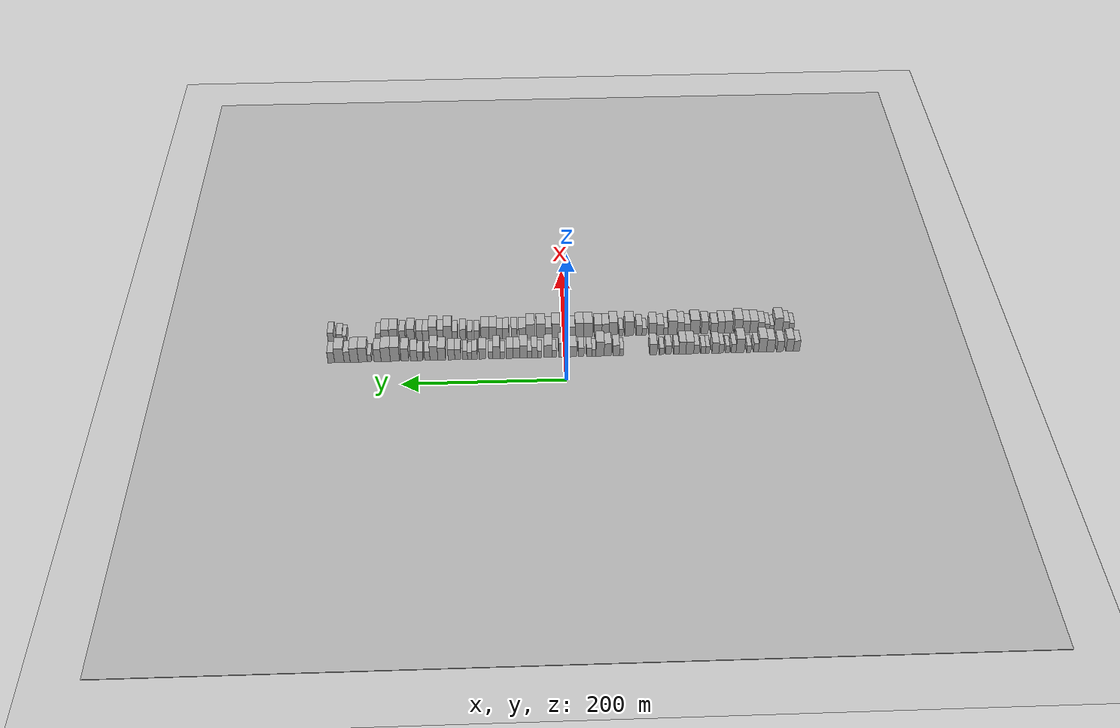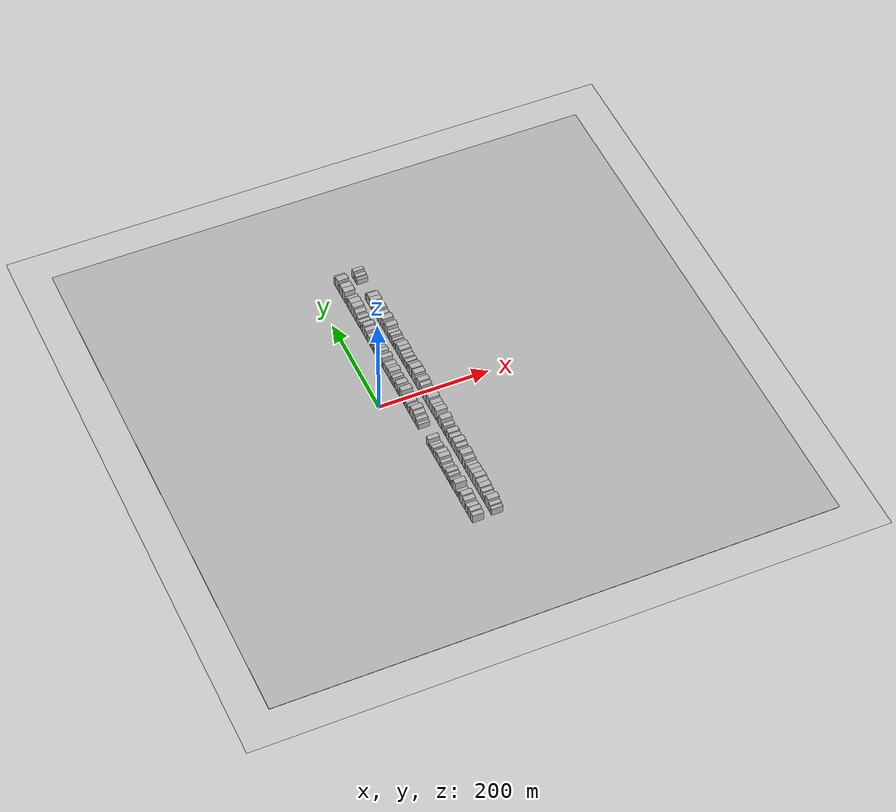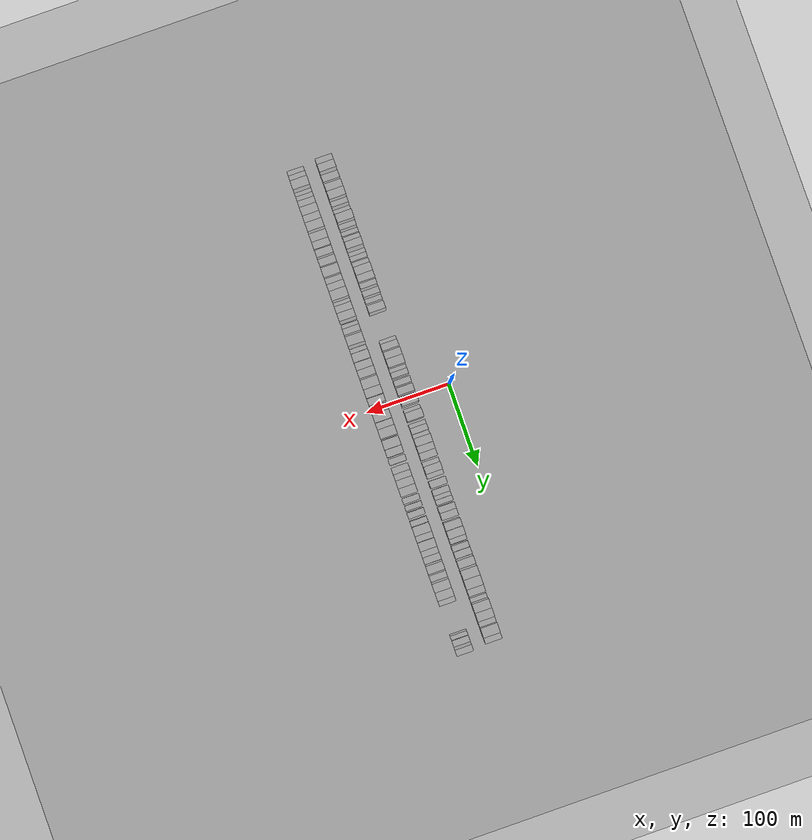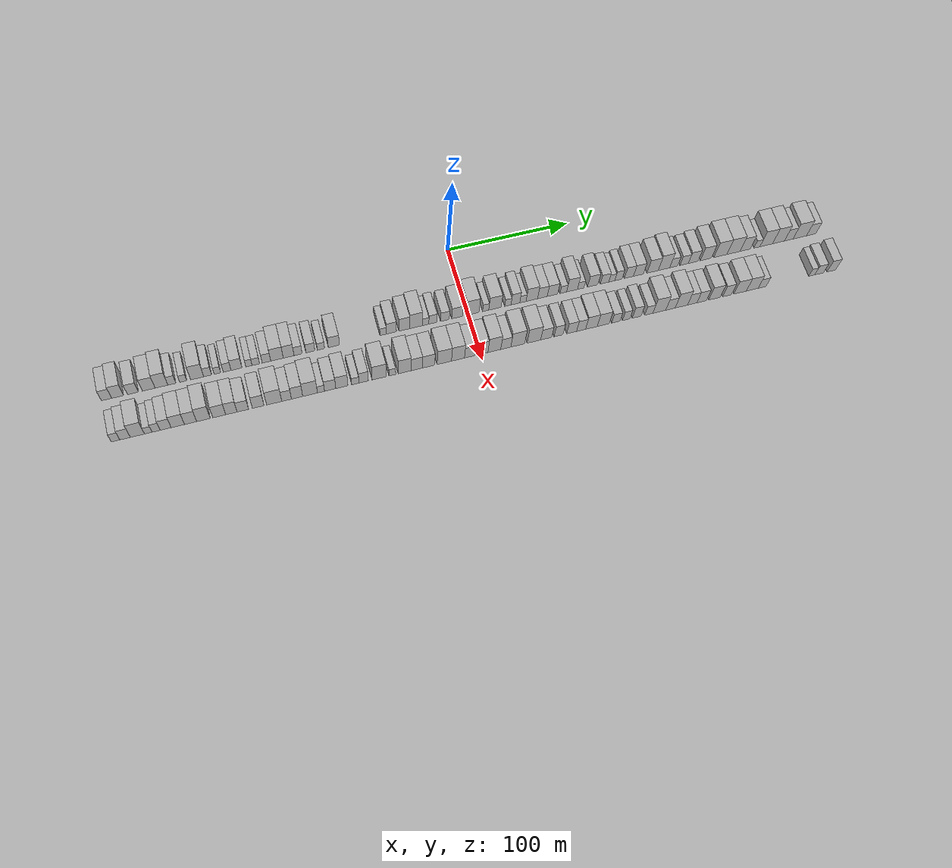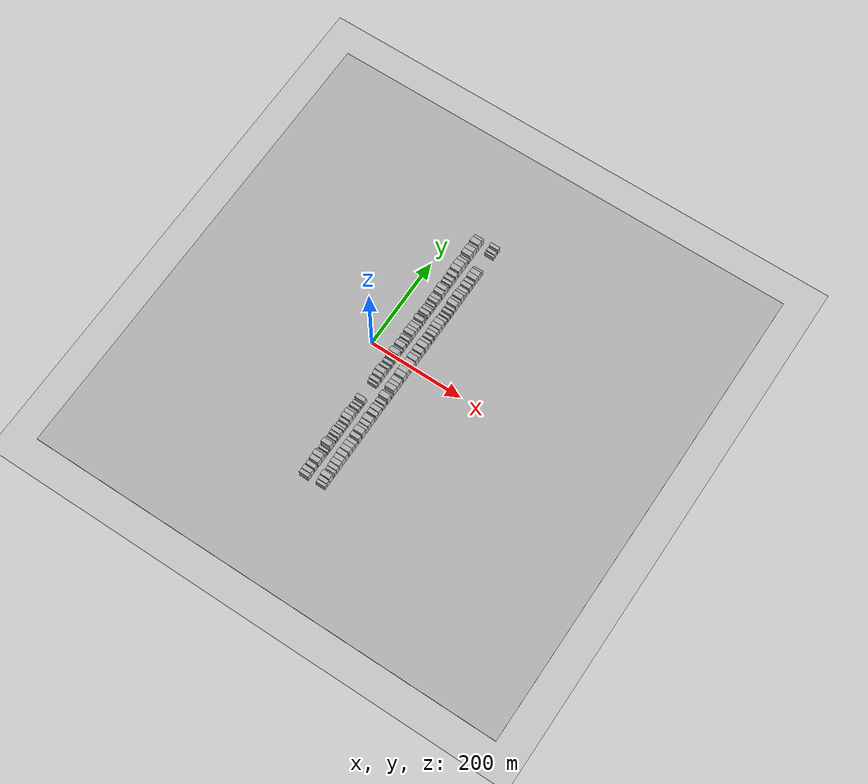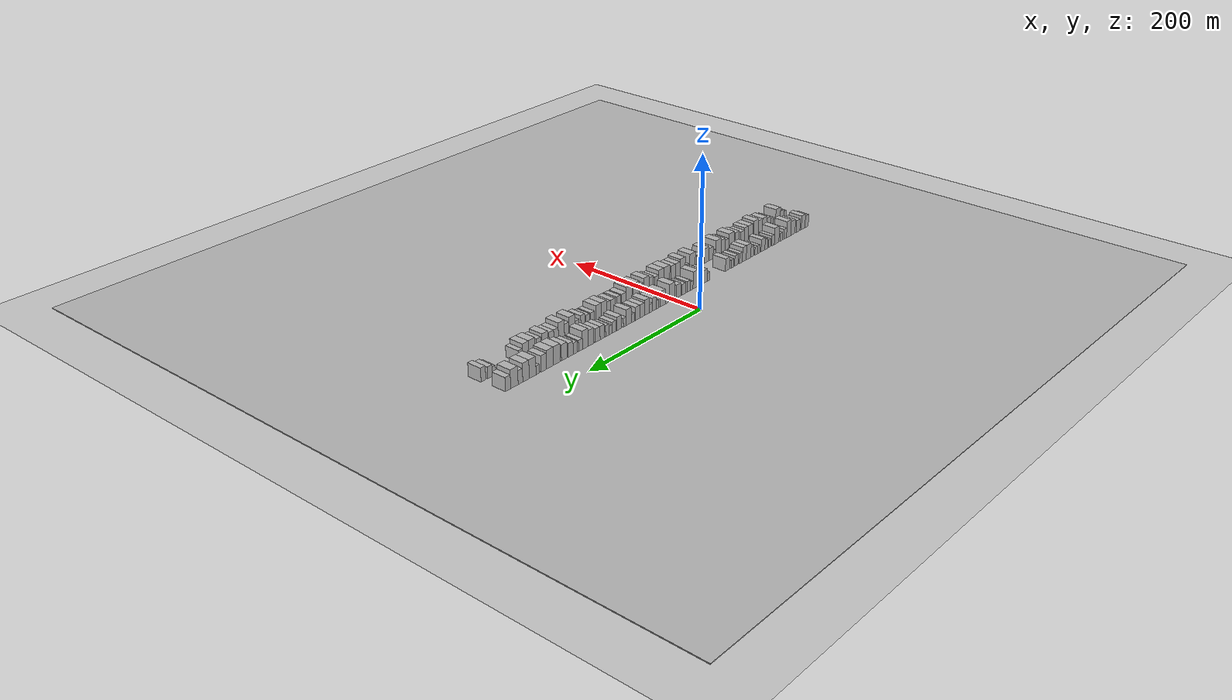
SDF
<?xml version="1.0" encoding="utf-8"?>

<sdf version="1.6">

   <world name="default">

      <gui fullscreen="0">

         <camera name="user_camera">

            <pose>-15 0 4.57585 0 0 0</pose>

            <view_controller>orbit</view_controller>

         </camera>

      </gui>

      <scene>

         <sky>

           <clouds>

             <speed>12</speed>

           </clouds>

         </sky>

         <ambient>0.4 0.4 0.4 1</ambient>

         <background>0.7 0.7 0.7 1</background>

         <shadows>1</shadows>

      </scene>

      <gravity>0 0 -9.8066</gravity>

      <magnetic_field>6e-06 2.3e-05 -4.2e-05</magnetic_field>

      <physics default="0" name="default_physics" type="ode">

         <ode>

            <solver>

               <type>quick</type>

               <iters>10</iters>

               <sor>1.0</sor>

               <use_dynamic_moi_rescaling>0</use_dynamic_moi_rescaling>

            </solver>

            <constraints>

               <cfm>0</cfm>

               <erp>0.2</erp>

               <contact_max_correcting_vel>100</contact_max_correcting_vel>

               <contact_surface_layer>0.001</contact_surface_layer>

            </constraints>

         </ode>

         <max_step_size>0.004</max_step_size>

         <real_time_factor>1</real_time_factor>

         <real_time_update_rate>250</real_time_update_rate>

      </physics>

      <light name="sun" type="directional">

         <cast_shadows>1</cast_shadows>

         <pose>0 0 10 0 0 0</pose>

         <diffuse>0.8 0.8 0.8 1</diffuse>

         <specular>0.2 0.2 0.2 1</specular>

         <attenuation>

            <range>1000</range>

            <constant>0.9</constant>

            <linear>0.01</linear>

            <quadratic>0.001</quadratic>

         </attenuation>

         <direction>-0.5 0.1 -0.9</direction>

      </light>

      <include>

         <name>ground_plane_1</name>

         <uri>model://HANNAS_ground_plane</uri>

         <pose>0 0 0  0 0 0</pose>

      </include>

      <include>

         <name>ground_plane_2</name>

         <uri>model://HANNAS_ground_plane</uri>

         <pose>100 0 0  0 0 0</pose>

      </include>

      <model name="building_1">

         <static>1</static>

         <pose frame="">50.0000 -286.0324 0 0.000000 0.000000 0.000000</pose>

         <link name="link">

            <pose frame="">0 0 9.00 0 0 0</pose>

            <collision name="collision">

               <geometry>

                  <box>

                     <size>20.0000 7.9351 18.0000</size>

                  </box>

               </geometry>

               <max_contacts>10</max_contacts>

               <surface>

                  <contact>

                     <ode/>

                  </contact>

                  <bounce/>

                  <friction>

                     <torsional>

                        <ode/>

                     </torsional>

                     <ode/>

                  </friction>

               </surface>

            </collision>

            <visual name="visual">

               <cast_shadows>0</cast_shadows>

               <geometry>

                  <box>

                     <size>20.0000 7.9351 18.0000</size>

                  </box>

               </geometry>

               <material>

                  <script>

                     <uri>model://HANNAS_wall/materials/scripts</uri>

                     <uri>model://HANNAS_wall/materials/textures</uri>

                     <name>vrc/HANNAS_wall</name>

                  </script>

               </material>

            </visual>

            <self_collide>0</self_collide>

            <enable_wind>0</enable_wind>

            <kinematic>0</kinematic>

         </link>

      </model>

      <model name="building_2">

         <static>1</static>

         <pose frame="">50.0000 -277.5326 0 0.000000 0.000000 0.000000</pose>

         <link name="link">

            <pose frame="">0 0 10.50 0 0 0</pose>

            <collision name="collision">

               <geometry>

                  <box>

                     <size>20.0000 9.0645 21.0000</size>

                  </box>

               </geometry>

               <max_contacts>10</max_contacts>

               <surface>

                  <contact>

                     <ode/>

                  </contact>

                  <bounce/>

                  <friction>

                     <torsional>

                        <ode/>

                     </torsional>

                     <ode/>

                  </friction>

               </surface>

            </collision>

            <visual name="visual">

               <cast_shadows>0</cast_shadows>

               <geometry>

                  <box>

                     <size>20.0000 9.0645 21.0000</size>

                  </box>

               </geometry>

               <material>

                  <script>

                     <uri>model://HANNAS_wall/materials/scripts</uri>

                     <uri>model://HANNAS_wall/materials/textures</uri>

                     <name>vrc/HANNAS_wall</name>

                  </script>

               </material>

            </visual>

            <self_collide>0</self_collide>

            <enable_wind>0</enable_wind>

            <kinematic>0</kinematic>

         </link>

      </model>

      <model name="building_3">

         <static>1</static>

         <pose frame="">50.0000 -265.7728 0 0.000000 0.000000 0.000000</pose>

         <link name="link">

            <pose frame="">0 0 9.00 0 0 0</pose>

            <collision name="collision">

               <geometry>

                  <box>

                     <size>20.0000 8.4551 18.0000</size>

                  </box>

               </geometry>

               <max_contacts>10</max_contacts>

               <surface>

                  <contact>

                     <ode/>

                  </contact>

                  <bounce/>

                  <friction>

                     <torsional>

                        <ode/>

                     </torsional>

                     <ode/>

                  </friction>

               </surface>

            </collision>

            <visual name="visual">

               <cast_shadows>0</cast_shadows>

               <geometry>

                  <box>

                     <size>20.0000 8.4551 18.0000</size>

                  </box>

               </geometry>

               <material>

                  <script>

                     <uri>model://HANNAS_wall/materials/scripts</uri>

                     <uri>model://HANNAS_wall/materials/textures</uri>

                     <name>vrc/HANNAS_wall</name>

                  </script>

               </material>

            </visual>

            <self_collide>0</self_collide>

            <enable_wind>0</enable_wind>

            <kinematic>0</kinematic>

         </link>

      </model>

      <model name="building_4">

         <static>1</static>

         <pose frame="">50.0000 -253.5943 0 0.000000 0.000000 0.000000</pose>

         <link name="link">

            <pose frame="">0 0 10.50 0 0 0</pose>

            <collision name="collision">

               <geometry>

                  <box>

                     <size>20.0000 9.9019 21.0000</size>

                  </box>

               </geometry>

               <max_contacts>10</max_contacts>

               <surface>

                  <contact>

                     <ode/>

                  </contact>

                  <bounce/>

                  <friction>

                     <torsional>

                        <ode/>

                     </torsional>

                     <ode/>

                  </friction>

               </surface>

            </collision>

            <visual name="visual">

               <cast_shadows>0</cast_shadows>

               <geometry>

                  <box>

                     <size>20.0000 9.9019 21.0000</size>

                  </box>

               </geometry>

               <material>

                  <script>

                     <uri>model://HANNAS_wall/materials/scripts</uri>

                     <uri>model://HANNAS_wall/materials/textures</uri>

                     <name>vrc/HANNAS_wall</name>

                  </script>

               </material>

            </visual>

            <self_collide>0</self_collide>

            <enable_wind>0</enable_wind>

            <kinematic>0</kinematic>

         </link>

      </model>

      <model name="building_5">

         <static>1</static>

         <pose frame="">50.0000 -243.7121 0 0.000000 0.000000 0.000000</pose>

         <link name="link">

            <pose frame="">0 0 12.00 0 0 0</pose>

            <collision name="collision">

               <geometry>

                  <box>

                     <size>20.0000 9.8626 24.0000</size>

                  </box>

               </geometry>

               <max_contacts>10</max_contacts>

               <surface>

                  <contact>

                     <ode/>

                  </contact>

                  <bounce/>

                  <friction>

                     <torsional>

                        <ode/>

                     </torsional>

                     <ode/>

                  </friction>

               </surface>

            </collision>

            <visual name="visual">

               <cast_shadows>0</cast_shadows>

               <geometry>

                  <box>

                     <size>20.0000 9.8626 24.0000</size>

                  </box>

               </geometry>

               <material>

                  <script>

                     <uri>model://HANNAS_wall/materials/scripts</uri>

                     <uri>model://HANNAS_wall/materials/textures</uri>

                     <name>vrc/HANNAS_wall</name>

                  </script>

               </material>

            </visual>

            <self_collide>0</self_collide>

            <enable_wind>0</enable_wind>

            <kinematic>0</kinematic>

         </link>

      </model>

      <model name="building_6">

         <static>1</static>

         <pose frame="">50.0000 -235.6950 0 0.000000 0.000000 0.000000</pose>

         <link name="link">

            <pose frame="">0 0 7.50 0 0 0</pose>

            <collision name="collision">

               <geometry>

                  <box>

                     <size>20.0000 6.1716 15.0000</size>

                  </box>

               </geometry>

               <max_contacts>10</max_contacts>

               <surface>

                  <contact>

                     <ode/>

                  </contact>

                  <bounce/>

                  <friction>

                     <torsional>

                        <ode/>

                     </torsional>

                     <ode/>

                  </friction>

               </surface>

            </collision>

            <visual name="visual">

               <cast_shadows>0</cast_shadows>

               <geometry>

                  <box>

                     <size>20.0000 6.1716 15.0000</size>

                  </box>

               </geometry>

               <material>

                  <script>

                     <uri>model://HANNAS_wall/materials/scripts</uri>

                     <uri>model://HANNAS_wall/materials/textures</uri>

                     <name>vrc/HANNAS_wall</name>

                  </script>

               </material>

            </visual>

            <self_collide>0</self_collide>

            <enable_wind>0</enable_wind>

            <kinematic>0</kinematic>

         </link>

      </model>

      <model name="building_7">

         <static>1</static>

         <pose frame="">50.0000 -226.8750 0 0.000000 0.000000 0.000000</pose>

         <link name="link">

            <pose frame="">0 0 6.00 0 0 0</pose>

            <collision name="collision">

               <geometry>

                  <box>

                     <size>20.0000 5.4686 12.0000</size>

                  </box>

               </geometry>

               <max_contacts>10</max_contacts>

               <surface>

                  <contact>

                     <ode/>

                  </contact>

                  <bounce/>

                  <friction>

                     <torsional>

                        <ode/>

                     </torsional>

                     <ode/>

                  </friction>

               </surface>

            </collision>

            <visual name="visual">

               <cast_shadows>0</cast_shadows>

               <geometry>

                  <box>

                     <size>20.0000 5.4686 12.0000</size>

                  </box>

               </geometry>

               <material>

                  <script>

                     <uri>model://HANNAS_wall/materials/scripts</uri>

                     <uri>model://HANNAS_wall/materials/textures</uri>

                     <name>vrc/HANNAS_wall</name>

                  </script>

               </material>

            </visual>

            <self_collide>0</self_collide>

            <enable_wind>0</enable_wind>

            <kinematic>0</kinematic>

         </link>

      </model>

      <model name="building_8">

         <static>1</static>

         <pose frame="">50.0000 -216.0352 0 0.000000 0.000000 0.000000</pose>

         <link name="link">

            <pose frame="">0 0 12.00 0 0 0</pose>

            <collision name="collision">

               <geometry>

                  <box>

                     <size>20.0000 10.2110 24.0000</size>

                  </box>

               </geometry>

               <max_contacts>10</max_contacts>

               <surface>

                  <contact>

                     <ode/>

                  </contact>

                  <bounce/>

                  <friction>

                     <torsional>

                        <ode/>

                     </torsional>

                     <ode/>

                  </friction>

               </surface>

            </collision>

            <visual name="visual">

               <cast_shadows>0</cast_shadows>

               <geometry>

                  <box>

                     <size>20.0000 10.2110 24.0000</size>

                  </box>

               </geometry>

               <material>

                  <script>

                     <uri>model://HANNAS_wall/materials/scripts</uri>

                     <uri>model://HANNAS_wall/materials/textures</uri>

                     <name>vrc/HANNAS_wall</name>

                  </script>

               </material>

            </visual>

            <self_collide>0</self_collide>

            <enable_wind>0</enable_wind>

            <kinematic>0</kinematic>

         </link>

      </model>

      <model name="building_9">

         <static>1</static>

         <pose frame="">50.0000 -207.8794 0 0.000000 0.000000 0.000000</pose>

         <link name="link">

            <pose frame="">0 0 7.50 0 0 0</pose>

            <collision name="collision">

               <geometry>

                  <box>

                     <size>20.0000 6.1006 15.0000</size>

                  </box>

               </geometry>

               <max_contacts>10</max_contacts>

               <surface>

                  <contact>

                     <ode/>

                  </contact>

                  <bounce/>

                  <friction>

                     <torsional>

                        <ode/>

                     </torsional>

                     <ode/>

                  </friction>

               </surface>

            </collision>

            <visual name="visual">

               <cast_shadows>0</cast_shadows>

               <geometry>

                  <box>

                     <size>20.0000 6.1006 15.0000</size>

                  </box>

               </geometry>

               <material>

                  <script>

                     <uri>model://HANNAS_wall/materials/scripts</uri>

                     <uri>model://HANNAS_wall/materials/textures</uri>

                     <name>vrc/HANNAS_wall</name>

                  </script>

               </material>

            </visual>

            <self_collide>0</self_collide>

            <enable_wind>0</enable_wind>

            <kinematic>0</kinematic>

         </link>

      </model>

      <model name="building_10">

         <static>1</static>

         <pose frame="">50.0000 -200.2772 0 0.000000 0.000000 0.000000</pose>

         <link name="link">

            <pose frame="">0 0 6.00 0 0 0</pose>

            <collision name="collision">

               <geometry>

                  <box>

                     <size>20.0000 5.1039 12.0000</size>

                  </box>

               </geometry>

               <max_contacts>10</max_contacts>

               <surface>

                  <contact>

                     <ode/>

                  </contact>

                  <bounce/>

                  <friction>

                     <torsional>

                        <ode/>

                     </torsional>

                     <ode/>

                  </friction>

               </surface>

            </collision>

            <visual name="visual">

               <cast_shadows>0</cast_shadows>

               <geometry>

                  <box>

                     <size>20.0000 5.1039 12.0000</size>

                  </box>

               </geometry>

               <material>

                  <script>

                     <uri>model://HANNAS_wall/materials/scripts</uri>

                     <uri>model://HANNAS_wall/materials/textures</uri>

                     <name>vrc/HANNAS_wall</name>

                  </script>

               </material>

            </visual>

            <self_collide>0</self_collide>

            <enable_wind>0</enable_wind>

            <kinematic>0</kinematic>

         </link>

      </model>

      <model name="building_11">

         <static>1</static>

         <pose frame="">50.0000 -192.6694 0 0.000000 0.000000 0.000000</pose>

         <link name="link">

            <pose frame="">0 0 7.50 0 0 0</pose>

            <collision name="collision">

               <geometry>

                  <box>

                     <size>20.0000 6.1117 15.0000</size>

                  </box>

               </geometry>

               <max_contacts>10</max_contacts>

               <surface>

                  <contact>

                     <ode/>

                  </contact>

                  <bounce/>

                  <friction>

                     <torsional>

                        <ode/>

                     </torsional>

                     <ode/>

                  </friction>

               </surface>

            </collision>

            <visual name="visual">

               <cast_shadows>0</cast_shadows>

               <geometry>

                  <box>

                     <size>20.0000 6.1117 15.0000</size>

                  </box>

               </geometry>

               <material>

                  <script>

                     <uri>model://HANNAS_wall/materials/scripts</uri>

                     <uri>model://HANNAS_wall/materials/textures</uri>

                     <name>vrc/HANNAS_wall</name>

                  </script>

               </material>

            </visual>

            <self_collide>0</self_collide>

            <enable_wind>0</enable_wind>

            <kinematic>0</kinematic>

         </link>

      </model>

      <model name="building_12">

         <static>1</static>

         <pose frame="">50.0000 -185.3379 0 0.000000 0.000000 0.000000</pose>

         <link name="link">

            <pose frame="">0 0 9.00 0 0 0</pose>

            <collision name="collision">

               <geometry>

                  <box>

                     <size>20.0000 8.5512 18.0000</size>

                  </box>

               </geometry>

               <max_contacts>10</max_contacts>

               <surface>

                  <contact>

                     <ode/>

                  </contact>

                  <bounce/>

                  <friction>

                     <torsional>

                        <ode/>

                     </torsional>

                     <ode/>

                  </friction>

               </surface>

            </collision>

            <visual name="visual">

               <cast_shadows>0</cast_shadows>

               <geometry>

                  <box>

                     <size>20.0000 8.5512 18.0000</size>

                  </box>

               </geometry>

               <material>

                  <script>

                     <uri>model://HANNAS_wall/materials/scripts</uri>

                     <uri>model://HANNAS_wall/materials/textures</uri>

                     <name>vrc/HANNAS_wall</name>

                  </script>

               </material>

            </visual>

            <self_collide>0</self_collide>

            <enable_wind>0</enable_wind>

            <kinematic>0</kinematic>

         </link>

      </model>

      <model name="building_13">

         <static>1</static>

         <pose frame="">50.0000 -175.5962 0 0.000000 0.000000 0.000000</pose>

         <link name="link">

            <pose frame="">0 0 6.00 0 0 0</pose>

            <collision name="collision">

               <geometry>

                  <box>

                     <size>20.0000 4.9323 12.0000</size>

                  </box>

               </geometry>

               <max_contacts>10</max_contacts>

               <surface>

                  <contact>

                     <ode/>

                  </contact>

                  <bounce/>

                  <friction>

                     <torsional>

                        <ode/>

                     </torsional>

                     <ode/>

                  </friction>

               </surface>

            </collision>

            <visual name="visual">

               <cast_shadows>0</cast_shadows>

               <geometry>

                  <box>

                     <size>20.0000 4.9323 12.0000</size>

                  </box>

               </geometry>

               <material>

                  <script>

                     <uri>model://HANNAS_wall/materials/scripts</uri>

                     <uri>model://HANNAS_wall/materials/textures</uri>

                     <name>vrc/HANNAS_wall</name>

                  </script>

               </material>

            </visual>

            <self_collide>0</self_collide>

            <enable_wind>0</enable_wind>

            <kinematic>0</kinematic>

         </link>

      </model>

      <model name="building_14">

         <static>1</static>

         <pose frame="">50.0000 -170.1926 0 0.000000 0.000000 0.000000</pose>

         <link name="link">

            <pose frame="">0 0 6.00 0 0 0</pose>

            <collision name="collision">

               <geometry>

                  <box>

                     <size>20.0000 5.8748 12.0000</size>

                  </box>

               </geometry>

               <max_contacts>10</max_contacts>

               <surface>

                  <contact>

                     <ode/>

                  </contact>

                  <bounce/>

                  <friction>

                     <torsional>

                        <ode/>

                     </torsional>

                     <ode/>

                  </friction>

               </surface>

            </collision>

            <visual name="visual">

               <cast_shadows>0</cast_shadows>

               <geometry>

                  <box>

                     <size>20.0000 5.8748 12.0000</size>

                  </box>

               </geometry>

               <material>

                  <script>

                     <uri>model://HANNAS_wall/materials/scripts</uri>

                     <uri>model://HANNAS_wall/materials/textures</uri>

                     <name>vrc/HANNAS_wall</name>

                  </script>

               </material>

            </visual>

            <self_collide>0</self_collide>

            <enable_wind>0</enable_wind>

            <kinematic>0</kinematic>

         </link>

      </model>

      <model name="building_15">

         <static>1</static>

         <pose frame="">50.0000 -161.8780 0 0.000000 0.000000 0.000000</pose>

         <link name="link">

            <pose frame="">0 0 7.50 0 0 0</pose>

            <collision name="collision">

               <geometry>

                  <box>

                     <size>20.0000 6.7544 15.0000</size>

                  </box>

               </geometry>

               <max_contacts>10</max_contacts>

               <surface>

                  <contact>

                     <ode/>

                  </contact>

                  <bounce/>

                  <friction>

                     <torsional>

                        <ode/>

                     </torsional>

                     <ode/>

                  </friction>

               </surface>

            </collision>

            <visual name="visual">

               <cast_shadows>0</cast_shadows>

               <geometry>

                  <box>

                     <size>20.0000 6.7544 15.0000</size>

                  </box>

               </geometry>

               <material>

                  <script>

                     <uri>model://HANNAS_wall/materials/scripts</uri>

                     <uri>model://HANNAS_wall/materials/textures</uri>

                     <name>vrc/HANNAS_wall</name>

                  </script>

               </material>

            </visual>

            <self_collide>0</self_collide>

            <enable_wind>0</enable_wind>

            <kinematic>0</kinematic>

         </link>

      </model>

      <model name="building_16">

         <static>1</static>

         <pose frame="">50.0000 -153.5488 0 0.000000 0.000000 0.000000</pose>

         <link name="link">

            <pose frame="">0 0 10.50 0 0 0</pose>

            <collision name="collision">

               <geometry>

                  <box>

                     <size>20.0000 9.9040 21.0000</size>

                  </box>

               </geometry>

               <max_contacts>10</max_contacts>

               <surface>

                  <contact>

                     <ode/>

                  </contact>

                  <bounce/>

                  <friction>

                     <torsional>

                        <ode/>

                     </torsional>

                     <ode/>

                  </friction>

               </surface>

            </collision>

            <visual name="visual">

               <cast_shadows>0</cast_shadows>

               <geometry>

                  <box>

                     <size>20.0000 9.9040 21.0000</size>

                  </box>

               </geometry>

               <material>

                  <script>

                     <uri>model://HANNAS_wall/materials/scripts</uri>

                     <uri>model://HANNAS_wall/materials/textures</uri>

                     <name>vrc/HANNAS_wall</name>

                  </script>

               </material>

            </visual>

            <self_collide>0</self_collide>

            <enable_wind>0</enable_wind>

            <kinematic>0</kinematic>

         </link>

      </model>

      <model name="building_17">

         <static>1</static>

         <pose frame="">50.0000 -144.3507 0 0.000000 0.000000 0.000000</pose>

         <link name="link">

            <pose frame="">0 0 10.50 0 0 0</pose>

            <collision name="collision">

               <geometry>

                  <box>

                     <size>20.0000 8.4921 21.0000</size>

                  </box>

               </geometry>

               <max_contacts>10</max_contacts>

               <surface>

                  <contact>

                     <ode/>

                  </contact>

                  <bounce/>

                  <friction>

                     <torsional>

                        <ode/>

                     </torsional>

                     <ode/>

                  </friction>

               </surface>

            </collision>

            <visual name="visual">

               <cast_shadows>0</cast_shadows>

               <geometry>

                  <box>

                     <size>20.0000 8.4921 21.0000</size>

                  </box>

               </geometry>

               <material>

                  <script>

                     <uri>model://HANNAS_wall/materials/scripts</uri>

                     <uri>model://HANNAS_wall/materials/textures</uri>

                     <name>vrc/HANNAS_wall</name>

                  </script>

               </material>

            </visual>

            <self_collide>0</self_collide>

            <enable_wind>0</enable_wind>

            <kinematic>0</kinematic>

         </link>

      </model>

      <model name="building_18">

         <static>1</static>

         <pose frame="">50.0000 -136.8926 0 0.000000 0.000000 0.000000</pose>

         <link name="link">

            <pose frame="">0 0 7.50 0 0 0</pose>

            <collision name="collision">

               <geometry>

                  <box>

                     <size>20.0000 6.4240 15.0000</size>

                  </box>

               </geometry>

               <max_contacts>10</max_contacts>

               <surface>

                  <contact>

                     <ode/>

                  </contact>

                  <bounce/>

                  <friction>

                     <torsional>

                        <ode/>

                     </torsional>

                     <ode/>

                  </friction>

               </surface>

            </collision>

            <visual name="visual">

               <cast_shadows>0</cast_shadows>

               <geometry>

                  <box>

                     <size>20.0000 6.4240 15.0000</size>

                  </box>

               </geometry>

               <material>

                  <script>

                     <uri>model://HANNAS_wall/materials/scripts</uri>

                     <uri>model://HANNAS_wall/materials/textures</uri>

                     <name>vrc/HANNAS_wall</name>

                  </script>

               </material>

            </visual>

            <self_collide>0</self_collide>

            <enable_wind>0</enable_wind>

            <kinematic>0</kinematic>

         </link>

      </model>

      <model name="building_19">

         <static>1</static>

         <pose frame="">50.0000 -127.1403 0 0.000000 0.000000 0.000000</pose>

         <link name="link">

            <pose frame="">0 0 7.50 0 0 0</pose>

            <collision name="collision">

               <geometry>

                  <box>

                     <size>20.0000 7.0807 15.0000</size>

                  </box>

               </geometry>

               <max_contacts>10</max_contacts>

               <surface>

                  <contact>

                     <ode/>

                  </contact>

                  <bounce/>

                  <friction>

                     <torsional>

                        <ode/>

                     </torsional>

                     <ode/>

                  </friction>

               </surface>

            </collision>

            <visual name="visual">

               <cast_shadows>0</cast_shadows>

               <geometry>

                  <box>

                     <size>20.0000 7.0807 15.0000</size>

                  </box>

               </geometry>

               <material>

                  <script>

                     <uri>model://HANNAS_wall/materials/scripts</uri>

                     <uri>model://HANNAS_wall/materials/textures</uri>

                     <name>vrc/HANNAS_wall</name>

                  </script>

               </material>

            </visual>

            <self_collide>0</self_collide>

            <enable_wind>0</enable_wind>

            <kinematic>0</kinematic>

         </link>

      </model>

      <model name="building_20">

         <static>1</static>

         <pose frame="">50.0000 -118.7447 0 0.000000 0.000000 0.000000</pose>

         <link name="link">

            <pose frame="">0 0 6.00 0 0 0</pose>

            <collision name="collision">

               <geometry>

                  <box>

                     <size>20.0000 5.7105 12.0000</size>

                  </box>

               </geometry>

               <max_contacts>10</max_contacts>

               <surface>

                  <contact>

                     <ode/>

                  </contact>

                  <bounce/>

                  <friction>

                     <torsional>

                        <ode/>

                     </torsional>

                     <ode/>

                  </friction>

               </surface>

            </collision>

            <visual name="visual">

               <cast_shadows>0</cast_shadows>

               <geometry>

                  <box>

                     <size>20.0000 5.7105 12.0000</size>

                  </box>

               </geometry>

               <material>

                  <script>

                     <uri>model://HANNAS_wall/materials/scripts</uri>

                     <uri>model://HANNAS_wall/materials/textures</uri>

                     <name>vrc/HANNAS_wall</name>

                  </script>

               </material>

            </visual>

            <self_collide>0</self_collide>

            <enable_wind>0</enable_wind>

            <kinematic>0</kinematic>

         </link>

      </model>

      <model name="building_21">

         <static>1</static>

         <pose frame="">50.0000 -108.4547 0 0.000000 0.000000 0.000000</pose>

         <link name="link">

            <pose frame="">0 0 9.00 0 0 0</pose>

            <collision name="collision">

               <geometry>

                  <box>

                     <size>20.0000 8.8697 18.0000</size>

                  </box>

               </geometry>

               <max_contacts>10</max_contacts>

               <surface>

                  <contact>

                     <ode/>

                  </contact>

                  <bounce/>

                  <friction>

                     <torsional>

                        <ode/>

                     </torsional>

                     <ode/>

                  </friction>

               </surface>

            </collision>

            <visual name="visual">

               <cast_shadows>0</cast_shadows>

               <geometry>

                  <box>

                     <size>20.0000 8.8697 18.0000</size>

                  </box>

               </geometry>

               <material>

                  <script>

                     <uri>model://HANNAS_wall/materials/scripts</uri>

                     <uri>model://HANNAS_wall/materials/textures</uri>

                     <name>vrc/HANNAS_wall</name>

                  </script>

               </material>

            </visual>

            <self_collide>0</self_collide>

            <enable_wind>0</enable_wind>

            <kinematic>0</kinematic>

         </link>

      </model>

      <model name="building_22">

         <static>1</static>

         <pose frame="">50.0000 -69.1038 0 0.000000 0.000000 0.000000</pose>

         <link name="link">

            <pose frame="">0 0 6.00 0 0 0</pose>

            <collision name="collision">

               <geometry>

                  <box>

                     <size>20.0000 5.2773 12.0000</size>

                  </box>

               </geometry>

               <max_contacts>10</max_contacts>

               <surface>

                  <contact>

                     <ode/>

                  </contact>

                  <bounce/>

                  <friction>

                     <torsional>

                        <ode/>

                     </torsional>

                     <ode/>

                  </friction>

               </surface>

            </collision>

            <visual name="visual">

               <cast_shadows>0</cast_shadows>

               <geometry>

                  <box>

                     <size>20.0000 5.2773 12.0000</size>

                  </box>

               </geometry>

               <material>

                  <script>

                     <uri>model://HANNAS_wall/materials/scripts</uri>

                     <uri>model://HANNAS_wall/materials/textures</uri>

                     <name>vrc/HANNAS_wall</name>

                  </script>

               </material>

            </visual>

            <self_collide>0</self_collide>

            <enable_wind>0</enable_wind>

            <kinematic>0</kinematic>

         </link>

      </model>

      <model name="building_23">

         <static>1</static>

         <pose frame="">50.0000 -62.4682 0 0.000000 0.000000 0.000000</pose>

         <link name="link">

            <pose frame="">0 0 9.00 0 0 0</pose>

            <collision name="collision">

               <geometry>

                  <box>

                     <size>20.0000 7.9938 18.0000</size>

                  </box>

               </geometry>

               <max_contacts>10</max_contacts>

               <surface>

                  <contact>

                     <ode/>

                  </contact>

                  <bounce/>

                  <friction>

                     <torsional>

                        <ode/>

                     </torsional>

                     <ode/>

                  </friction>

               </surface>

            </collision>

            <visual name="visual">

               <cast_shadows>0</cast_shadows>

               <geometry>

                  <box>

                     <size>20.0000 7.9938 18.0000</size>

                  </box>

               </geometry>

               <material>

                  <script>

                     <uri>model://HANNAS_wall/materials/scripts</uri>

                     <uri>model://HANNAS_wall/materials/textures</uri>

                     <name>vrc/HANNAS_wall</name>

                  </script>

               </material>

            </visual>

            <self_collide>0</self_collide>

            <enable_wind>0</enable_wind>

            <kinematic>0</kinematic>

         </link>

      </model>

      <model name="building_24">

         <static>1</static>

         <pose frame="">50.0000 -52.0570 0 0.000000 0.000000 0.000000</pose>

         <link name="link">

            <pose frame="">0 0 10.50 0 0 0</pose>

            <collision name="collision">

               <geometry>

                  <box>

                     <size>20.0000 8.8287 21.0000</size>

                  </box>

               </geometry>

               <max_contacts>10</max_contacts>

               <surface>

                  <contact>

                     <ode/>

                  </contact>

                  <bounce/>

                  <friction>

                     <torsional>

                        <ode/>

                     </torsional>

                     <ode/>

                  </friction>

               </surface>

            </collision>

            <visual name="visual">

               <cast_shadows>0</cast_shadows>

               <geometry>

                  <box>

                     <size>20.0000 8.8287 21.0000</size>

                  </box>

               </geometry>

               <material>

                  <script>

                     <uri>model://HANNAS_wall/materials/scripts</uri>

                     <uri>model://HANNAS_wall/materials/textures</uri>

                     <name>vrc/HANNAS_wall</name>

                  </script>

               </material>

            </visual>

            <self_collide>0</self_collide>

            <enable_wind>0</enable_wind>

            <kinematic>0</kinematic>

         </link>

      </model>

      <model name="building_25">

         <static>1</static>

         <pose frame="">50.0000 -42.5791 0 0.000000 0.000000 0.000000</pose>

         <link name="link">

            <pose frame="">0 0 12.00 0 0 0</pose>

            <collision name="collision">

               <geometry>

                  <box>

                     <size>20.0000 10.1271 24.0000</size>

                  </box>

               </geometry>

               <max_contacts>10</max_contacts>

               <surface>

                  <contact>

                     <ode/>

                  </contact>

                  <bounce/>

                  <friction>

                     <torsional>

                        <ode/>

                     </torsional>

                     <ode/>

                  </friction>

               </surface>

            </collision>

            <visual name="visual">

               <cast_shadows>0</cast_shadows>

               <geometry>

                  <box>

                     <size>20.0000 10.1271 24.0000</size>

                  </box>

               </geometry>

               <material>

                  <script>

                     <uri>model://HANNAS_wall/materials/scripts</uri>

                     <uri>model://HANNAS_wall/materials/textures</uri>

                     <name>vrc/HANNAS_wall</name>

                  </script>

               </material>

            </visual>

            <self_collide>0</self_collide>

            <enable_wind>0</enable_wind>

            <kinematic>0</kinematic>

         </link>

      </model>

      <model name="building_26">

         <static>1</static>

         <pose frame="">50.0000 -34.9127 0 0.000000 0.000000 0.000000</pose>

         <link name="link">

            <pose frame="">0 0 6.00 0 0 0</pose>

            <collision name="collision">

               <geometry>

                  <box>

                     <size>20.0000 5.2056 12.0000</size>

                  </box>

               </geometry>

               <max_contacts>10</max_contacts>

               <surface>

                  <contact>

                     <ode/>

                  </contact>

                  <bounce/>

                  <friction>

                     <torsional>

                        <ode/>

                     </torsional>

                     <ode/>

                  </friction>

               </surface>

            </collision>

            <visual name="visual">

               <cast_shadows>0</cast_shadows>

               <geometry>

                  <box>

                     <size>20.0000 5.2056 12.0000</size>

                  </box>

               </geometry>

               <material>

                  <script>

                     <uri>model://HANNAS_wall/materials/scripts</uri>

                     <uri>model://HANNAS_wall/materials/textures</uri>

                     <name>vrc/HANNAS_wall</name>

                  </script>

               </material>

            </visual>

            <self_collide>0</self_collide>

            <enable_wind>0</enable_wind>

            <kinematic>0</kinematic>

         </link>

      </model>

      <model name="building_27">

         <static>1</static>

         <pose frame="">50.0000 -29.0377 0 0.000000 0.000000 0.000000</pose>

         <link name="link">

            <pose frame="">0 0 7.50 0 0 0</pose>

            <collision name="collision">

               <geometry>

                  <box>

                     <size>20.0000 6.5444 15.0000</size>

                  </box>

               </geometry>

               <max_contacts>10</max_contacts>

               <surface>

                  <contact>

                     <ode/>

                  </contact>

                  <bounce/>

                  <friction>

                     <torsional>

                        <ode/>

                     </torsional>

                     <ode/>

                  </friction>

               </surface>

            </collision>

            <visual name="visual">

               <cast_shadows>0</cast_shadows>

               <geometry>

                  <box>

                     <size>20.0000 6.5444 15.0000</size>

                  </box>

               </geometry>

               <material>

                  <script>

                     <uri>model://HANNAS_wall/materials/scripts</uri>

                     <uri>model://HANNAS_wall/materials/textures</uri>

                     <name>vrc/HANNAS_wall</name>

                  </script>

               </material>

            </visual>

            <self_collide>0</self_collide>

            <enable_wind>0</enable_wind>

            <kinematic>0</kinematic>

         </link>

      </model>

      <model name="building_28">

         <static>1</static>

         <pose frame="">50.0000 -19.2700 0 0.000000 0.000000 0.000000</pose>

         <link name="link">

            <pose frame="">0 0 7.50 0 0 0</pose>

            <collision name="collision">

               <geometry>

                  <box>

                     <size>20.0000 6.9911 15.0000</size>

                  </box>

               </geometry>

               <max_contacts>10</max_contacts>

               <surface>

                  <contact>

                     <ode/>

                  </contact>

                  <bounce/>

                  <friction>

                     <torsional>

                        <ode/>

                     </torsional>

                     <ode/>

                  </friction>

               </surface>

            </collision>

            <visual name="visual">

               <cast_shadows>0</cast_shadows>

               <geometry>

                  <box>

                     <size>20.0000 6.9911 15.0000</size>

                  </box>

               </geometry>

               <material>

                  <script>

                     <uri>model://HANNAS_wall/materials/scripts</uri>

                     <uri>model://HANNAS_wall/materials/textures</uri>

                     <name>vrc/HANNAS_wall</name>

                  </script>

               </material>

            </visual>

            <self_collide>0</self_collide>

            <enable_wind>0</enable_wind>

            <kinematic>0</kinematic>

         </link>

      </model>

      <model name="building_29">

         <static>1</static>

         <pose frame="">50.0000 -9.3897 0 0.000000 0.000000 0.000000</pose>

         <link name="link">

            <pose frame="">0 0 9.00 0 0 0</pose>

            <collision name="collision">

               <geometry>

                  <box>

                     <size>20.0000 8.7695 18.0000</size>

                  </box>

               </geometry>

               <max_contacts>10</max_contacts>

               <surface>

                  <contact>

                     <ode/>

                  </contact>

                  <bounce/>

                  <friction>

                     <torsional>

                        <ode/>

                     </torsional>

                     <ode/>

                  </friction>

               </surface>

            </collision>

            <visual name="visual">

               <cast_shadows>0</cast_shadows>

               <geometry>

                  <box>

                     <size>20.0000 8.7695 18.0000</size>

                  </box>

               </geometry>

               <material>

                  <script>

                     <uri>model://HANNAS_wall/materials/scripts</uri>

                     <uri>model://HANNAS_wall/materials/textures</uri>

                     <name>vrc/HANNAS_wall</name>

                  </script>

               </material>

            </visual>

            <self_collide>0</self_collide>

            <enable_wind>0</enable_wind>

            <kinematic>0</kinematic>

         </link>

      </model>

      <model name="building_30">

         <static>1</static>

         <pose frame="">50.0000 3.2112 0 0.000000 0.000000 0.000000</pose>

         <link name="link">

            <pose frame="">0 0 12.00 0 0 0</pose>

            <collision name="collision">

               <geometry>

                  <box>

                     <size>20.0000 10.4323 24.0000</size>

                  </box>

               </geometry>

               <max_contacts>10</max_contacts>

               <surface>

                  <contact>

                     <ode/>

                  </contact>

                  <bounce/>

                  <friction>

                     <torsional>

                        <ode/>

                     </torsional>

                     <ode/>

                  </friction>

               </surface>

            </collision>

            <visual name="visual">

               <cast_shadows>0</cast_shadows>

               <geometry>

                  <box>

                     <size>20.0000 10.4323 24.0000</size>

                  </box>

               </geometry>

               <material>

                  <script>

                     <uri>model://HANNAS_wall/materials/scripts</uri>

                     <uri>model://HANNAS_wall/materials/textures</uri>

                     <name>vrc/HANNAS_wall</name>

                  </script>

               </material>

            </visual>

            <self_collide>0</self_collide>

            <enable_wind>0</enable_wind>

            <kinematic>0</kinematic>

         </link>

      </model>

      <model name="building_31">

         <static>1</static>

         <pose frame="">50.0000 13.9062 0 0.000000 0.000000 0.000000</pose>

         <link name="link">

            <pose frame="">0 0 6.00 0 0 0</pose>

            <collision name="collision">

               <geometry>

                  <box>

                     <size>20.0000 4.9577 12.0000</size>

                  </box>

               </geometry>

               <max_contacts>10</max_contacts>

               <surface>

                  <contact>

                     <ode/>

                  </contact>

                  <bounce/>

                  <friction>

                     <torsional>

                        <ode/>

                     </torsional>

                     <ode/>

                  </friction>

               </surface>

            </collision>

            <visual name="visual">

               <cast_shadows>0</cast_shadows>

               <geometry>

                  <box>

                     <size>20.0000 4.9577 12.0000</size>

                  </box>

               </geometry>

               <material>

                  <script>

                     <uri>model://HANNAS_wall/materials/scripts</uri>

                     <uri>model://HANNAS_wall/materials/textures</uri>

                     <name>vrc/HANNAS_wall</name>

                  </script>

               </material>

            </visual>

            <self_collide>0</self_collide>

            <enable_wind>0</enable_wind>

            <kinematic>0</kinematic>

         </link>

      </model>

      <model name="building_32">

         <static>1</static>

         <pose frame="">50.0000 21.4622 0 0.000000 0.000000 0.000000</pose>

         <link name="link">

            <pose frame="">0 0 10.50 0 0 0</pose>

            <collision name="collision">

               <geometry>

                  <box>

                     <size>20.0000 10.1544 21.0000</size>

                  </box>

               </geometry>

               <max_contacts>10</max_contacts>

               <surface>

                  <contact>

                     <ode/>

                  </contact>

                  <bounce/>

                  <friction>

                     <torsional>

                        <ode/>

                     </torsional>

                     <ode/>

                  </friction>

               </surface>

            </collision>

            <visual name="visual">

               <cast_shadows>0</cast_shadows>

               <geometry>

                  <box>

                     <size>20.0000 10.1544 21.0000</size>

                  </box>

               </geometry>

               <material>

                  <script>

                     <uri>model://HANNAS_wall/materials/scripts</uri>

                     <uri>model://HANNAS_wall/materials/textures</uri>

                     <name>vrc/HANNAS_wall</name>

                  </script>

               </material>

            </visual>

            <self_collide>0</self_collide>

            <enable_wind>0</enable_wind>

            <kinematic>0</kinematic>

         </link>

      </model>

      <model name="building_33">

         <static>1</static>

         <pose frame="">50.0000 32.0887 0 0.000000 0.000000 0.000000</pose>

         <link name="link">

            <pose frame="">0 0 6.00 0 0 0</pose>

            <collision name="collision">

               <geometry>

                  <box>

                     <size>20.0000 5.0985 12.0000</size>

                  </box>

               </geometry>

               <max_contacts>10</max_contacts>

               <surface>

                  <contact>

                     <ode/>

                  </contact>

                  <bounce/>

                  <friction>

                     <torsional>

                        <ode/>

                     </torsional>

                     <ode/>

                  </friction>

               </surface>

            </collision>

            <visual name="visual">

               <cast_shadows>0</cast_shadows>

               <geometry>

                  <box>

                     <size>20.0000 5.0985 12.0000</size>

                  </box>

               </geometry>

               <material>

                  <script>

                     <uri>model://HANNAS_wall/materials/scripts</uri>

                     <uri>model://HANNAS_wall/materials/textures</uri>

                     <name>vrc/HANNAS_wall</name>

                  </script>

               </material>

            </visual>

            <self_collide>0</self_collide>

            <enable_wind>0</enable_wind>

            <kinematic>0</kinematic>

         </link>

      </model>

      <model name="building_34">

         <static>1</static>

         <pose frame="">50.0000 38.2567 0 0.000000 0.000000 0.000000</pose>

         <link name="link">

            <pose frame="">0 0 9.00 0 0 0</pose>

            <collision name="collision">

               <geometry>

                  <box>

                     <size>20.0000 7.2375 18.0000</size>

                  </box>

               </geometry>

               <max_contacts>10</max_contacts>

               <surface>

                  <contact>

                     <ode/>

                  </contact>

                  <bounce/>

                  <friction>

                     <torsional>

                        <ode/>

                     </torsional>

                     <ode/>

                  </friction>

               </surface>

            </collision>

            <visual name="visual">

               <cast_shadows>0</cast_shadows>

               <geometry>

                  <box>

                     <size>20.0000 7.2375 18.0000</size>

                  </box>

               </geometry>

               <material>

                  <script>

                     <uri>model://HANNAS_wall/materials/scripts</uri>

                     <uri>model://HANNAS_wall/materials/textures</uri>

                     <name>vrc/HANNAS_wall</name>

                  </script>

               </material>

            </visual>

            <self_collide>0</self_collide>

            <enable_wind>0</enable_wind>

            <kinematic>0</kinematic>

         </link>

      </model>

      <model name="building_35">

         <static>1</static>

         <pose frame="">50.0000 44.4460 0 0.000000 0.000000 0.000000</pose>

         <link name="link">

            <pose frame="">0 0 6.00 0 0 0</pose>

            <collision name="collision">

               <geometry>

                  <box>

                     <size>20.0000 5.1411 12.0000</size>

                  </box>

               </geometry>

               <max_contacts>10</max_contacts>

               <surface>

                  <contact>

                     <ode/>

                  </contact>

                  <bounce/>

                  <friction>

                     <torsional>

                        <ode/>

                     </torsional>

                     <ode/>

                  </friction>

               </surface>

            </collision>

            <visual name="visual">

               <cast_shadows>0</cast_shadows>

               <geometry>

                  <box>

                     <size>20.0000 5.1411 12.0000</size>

                  </box>

               </geometry>

               <material>

                  <script>

                     <uri>model://HANNAS_wall/materials/scripts</uri>

                     <uri>model://HANNAS_wall/materials/textures</uri>

                     <name>vrc/HANNAS_wall</name>

                  </script>

               </material>

            </visual>

            <self_collide>0</self_collide>

            <enable_wind>0</enable_wind>

            <kinematic>0</kinematic>

         </link>

      </model>

      <model name="building_36">

         <static>1</static>

         <pose frame="">50.0000 51.7506 0 0.000000 0.000000 0.000000</pose>

         <link name="link">

            <pose frame="">0 0 10.50 0 0 0</pose>

            <collision name="collision">

               <geometry>

                  <box>

                     <size>20.0000 9.4679 21.0000</size>

                  </box>

               </geometry>

               <max_contacts>10</max_contacts>

               <surface>

                  <contact>

                     <ode/>

                  </contact>

                  <bounce/>

                  <friction>

                     <torsional>

                        <ode/>

                     </torsional>

                     <ode/>

                  </friction>

               </surface>

            </collision>

            <visual name="visual">

               <cast_shadows>0</cast_shadows>

               <geometry>

                  <box>

                     <size>20.0000 9.4679 21.0000</size>

                  </box>

               </geometry>

               <material>

                  <script>

                     <uri>model://HANNAS_wall/materials/scripts</uri>

                     <uri>model://HANNAS_wall/materials/textures</uri>

                     <name>vrc/HANNAS_wall</name>

                  </script>

               </material>

            </visual>

            <self_collide>0</self_collide>

            <enable_wind>0</enable_wind>

            <kinematic>0</kinematic>

         </link>

      </model>

      <model name="building_37">

         <static>1</static>

         <pose frame="">50.0000 60.5005 0 0.000000 0.000000 0.000000</pose>

         <link name="link">

            <pose frame="">0 0 9.00 0 0 0</pose>

            <collision name="collision">

               <geometry>

                  <box>

                     <size>20.0000 8.0320 18.0000</size>

                  </box>

               </geometry>

               <max_contacts>10</max_contacts>

               <surface>

                  <contact>

                     <ode/>

                  </contact>

                  <bounce/>

                  <friction>

                     <torsional>

                        <ode/>

                     </torsional>

                     <ode/>

                  </friction>

               </surface>

            </collision>

            <visual name="visual">

               <cast_shadows>0</cast_shadows>

               <geometry>

                  <box>

                     <size>20.0000 8.0320 18.0000</size>

                  </box>

               </geometry>

               <material>

                  <script>

                     <uri>model://HANNAS_wall/materials/scripts</uri>

                     <uri>model://HANNAS_wall/materials/textures</uri>

                     <name>vrc/HANNAS_wall</name>

                  </script>

               </material>

            </visual>

            <self_collide>0</self_collide>

            <enable_wind>0</enable_wind>

            <kinematic>0</kinematic>

         </link>

      </model>

      <model name="building_38">

         <static>1</static>

         <pose frame="">50.0000 68.7919 0 0.000000 0.000000 0.000000</pose>

         <link name="link">

            <pose frame="">0 0 9.00 0 0 0</pose>

            <collision name="collision">

               <geometry>

                  <box>

                     <size>20.0000 8.5508 18.0000</size>

                  </box>

               </geometry>

               <max_contacts>10</max_contacts>

               <surface>

                  <contact>

                     <ode/>

                  </contact>

                  <bounce/>

                  <friction>

                     <torsional>

                        <ode/>

                     </torsional>

                     <ode/>

                  </friction>

               </surface>

            </collision>

            <visual name="visual">

               <cast_shadows>0</cast_shadows>

               <geometry>

                  <box>

                     <size>20.0000 8.5508 18.0000</size>

                  </box>

               </geometry>

               <material>

                  <script>

                     <uri>model://HANNAS_wall/materials/scripts</uri>

                     <uri>model://HANNAS_wall/materials/textures</uri>

                     <name>vrc/HANNAS_wall</name>

                  </script>

               </material>

            </visual>

            <self_collide>0</self_collide>

            <enable_wind>0</enable_wind>

            <kinematic>0</kinematic>

         </link>

      </model>

      <model name="building_39">

         <static>1</static>

         <pose frame="">50.0000 77.8318 0 0.000000 0.000000 0.000000</pose>

         <link name="link">

            <pose frame="">0 0 6.00 0 0 0</pose>

            <collision name="collision">

               <geometry>

                  <box>

                     <size>20.0000 5.5289 12.0000</size>

                  </box>

               </geometry>

               <max_contacts>10</max_contacts>

               <surface>

                  <contact>

                     <ode/>

                  </contact>

                  <bounce/>

                  <friction>

                     <torsional>

                        <ode/>

                     </torsional>

                     <ode/>

                  </friction>

               </surface>

            </collision>

            <visual name="visual">

               <cast_shadows>0</cast_shadows>

               <geometry>

                  <box>

                     <size>20.0000 5.5289 12.0000</size>

                  </box>

               </geometry>

               <material>

                  <script>

                     <uri>model://HANNAS_wall/materials/scripts</uri>

                     <uri>model://HANNAS_wall/materials/textures</uri>

                     <name>vrc/HANNAS_wall</name>

                  </script>

               </material>

            </visual>

            <self_collide>0</self_collide>

            <enable_wind>0</enable_wind>

            <kinematic>0</kinematic>

         </link>

      </model>

      <model name="building_40">

         <static>1</static>

         <pose frame="">50.0000 85.0678 0 0.000000 0.000000 0.000000</pose>

         <link name="link">

            <pose frame="">0 0 10.50 0 0 0</pose>

            <collision name="collision">

               <geometry>

                  <box>

                     <size>20.0000 8.9433 21.0000</size>

                  </box>

               </geometry>

               <max_contacts>10</max_contacts>

               <surface>

                  <contact>

                     <ode/>

                  </contact>

                  <bounce/>

                  <friction>

                     <torsional>

                        <ode/>

                     </torsional>

                     <ode/>

                  </friction>

               </surface>

            </collision>

            <visual name="visual">

               <cast_shadows>0</cast_shadows>

               <geometry>

                  <box>

                     <size>20.0000 8.9433 21.0000</size>

                  </box>

               </geometry>

               <material>

                  <script>

                     <uri>model://HANNAS_wall/materials/scripts</uri>

                     <uri>model://HANNAS_wall/materials/textures</uri>

                     <name>vrc/HANNAS_wall</name>

                  </script>

               </material>

            </visual>

            <self_collide>0</self_collide>

            <enable_wind>0</enable_wind>

            <kinematic>0</kinematic>

         </link>

      </model>

      <model name="building_41">

         <static>1</static>

         <pose frame="">50.0000 92.2608 0 0.000000 0.000000 0.000000</pose>

         <link name="link">

            <pose frame="">0 0 6.00 0 0 0</pose>

            <collision name="collision">

               <geometry>

                  <box>

                     <size>20.0000 5.4427 12.0000</size>

                  </box>

               </geometry>

               <max_contacts>10</max_contacts>

               <surface>

                  <contact>

                     <ode/>

                  </contact>

                  <bounce/>

                  <friction>

                     <torsional>

                        <ode/>

                     </torsional>

                     <ode/>

                  </friction>

               </surface>

            </collision>

            <visual name="visual">

               <cast_shadows>0</cast_shadows>

               <geometry>

                  <box>

                     <size>20.0000 5.4427 12.0000</size>

                  </box>

               </geometry>

               <material>

                  <script>

                     <uri>model://HANNAS_wall/materials/scripts</uri>

                     <uri>model://HANNAS_wall/materials/textures</uri>

                     <name>vrc/HANNAS_wall</name>

                  </script>

               </material>

            </visual>

            <self_collide>0</self_collide>

            <enable_wind>0</enable_wind>

            <kinematic>0</kinematic>

         </link>

      </model>

      <model name="building_42">

         <static>1</static>

         <pose frame="">50.0000 102.2842 0 0.000000 0.000000 0.000000</pose>

         <link name="link">

            <pose frame="">0 0 9.00 0 0 0</pose>

            <collision name="collision">

               <geometry>

                  <box>

                     <size>20.0000 8.6041 18.0000</size>

                  </box>

               </geometry>

               <max_contacts>10</max_contacts>

               <surface>

                  <contact>

                     <ode/>

                  </contact>

                  <bounce/>

                  <friction>

                     <torsional>

                        <ode/>

                     </torsional>

                     <ode/>

                  </friction>

               </surface>

            </collision>

            <visual name="visual">

               <cast_shadows>0</cast_shadows>

               <geometry>

                  <box>

                     <size>20.0000 8.6041 18.0000</size>

                  </box>

               </geometry>

               <material>

                  <script>

                     <uri>model://HANNAS_wall/materials/scripts</uri>

                     <uri>model://HANNAS_wall/materials/textures</uri>

                     <name>vrc/HANNAS_wall</name>

                  </script>

               </material>

            </visual>

            <self_collide>0</self_collide>

            <enable_wind>0</enable_wind>

            <kinematic>0</kinematic>

         </link>

      </model>

      <model name="building_43">

         <static>1</static>

         <pose frame="">50.0000 112.1249 0 0.000000 0.000000 0.000000</pose>

         <link name="link">

            <pose frame="">0 0 7.50 0 0 0</pose>

            <collision name="collision">

               <geometry>

                  <box>

                     <size>20.0000 7.0772 15.0000</size>

                  </box>

               </geometry>

               <max_contacts>10</max_contacts>

               <surface>

                  <contact>

                     <ode/>

                  </contact>

                  <bounce/>

                  <friction>

                     <torsional>

                        <ode/>

                     </torsional>

                     <ode/>

                  </friction>

               </surface>

            </collision>

            <visual name="visual">

               <cast_shadows>0</cast_shadows>

               <geometry>

                  <box>

                     <size>20.0000 7.0772 15.0000</size>

                  </box>

               </geometry>

               <material>

                  <script>

                     <uri>model://HANNAS_wall/materials/scripts</uri>

                     <uri>model://HANNAS_wall/materials/textures</uri>

                     <name>vrc/HANNAS_wall</name>

                  </script>

               </material>

            </visual>

            <self_collide>0</self_collide>

            <enable_wind>0</enable_wind>

            <kinematic>0</kinematic>

         </link>

      </model>

      <model name="building_44">

         <static>1</static>

         <pose frame="">50.0000 118.1817 0 0.000000 0.000000 0.000000</pose>

         <link name="link">

            <pose frame="">0 0 6.00 0 0 0</pose>

            <collision name="collision">

               <geometry>

                  <box>

                     <size>20.0000 5.0364 12.0000</size>

                  </box>

               </geometry>

               <max_contacts>10</max_contacts>

               <surface>

                  <contact>

                     <ode/>

                  </contact>

                  <bounce/>

                  <friction>

                     <torsional>

                        <ode/>

                     </torsional>

                     <ode/>

                  </friction>

               </surface>

            </collision>

            <visual name="visual">

               <cast_shadows>0</cast_shadows>

               <geometry>

                  <box>

                     <size>20.0000 5.0364 12.0000</size>

                  </box>

               </geometry>

               <material>

                  <script>

                     <uri>model://HANNAS_wall/materials/scripts</uri>

                     <uri>model://HANNAS_wall/materials/textures</uri>

                     <name>vrc/HANNAS_wall</name>

                  </script>

               </material>

            </visual>

            <self_collide>0</self_collide>

            <enable_wind>0</enable_wind>

            <kinematic>0</kinematic>

         </link>

      </model>

      <model name="building_45">

         <static>1</static>

         <pose frame="">50.0000 123.7220 0 0.000000 0.000000 0.000000</pose>

         <link name="link">

            <pose frame="">0 0 7.50 0 0 0</pose>

            <collision name="collision">

               <geometry>

                  <box>

                     <size>20.0000 6.0442 15.0000</size>

                  </box>

               </geometry>

               <max_contacts>10</max_contacts>

               <surface>

                  <contact>

                     <ode/>

                  </contact>

                  <bounce/>

                  <friction>

                     <torsional>

                        <ode/>

                     </torsional>

                     <ode/>

                  </friction>

               </surface>

            </collision>

            <visual name="visual">

               <cast_shadows>0</cast_shadows>

               <geometry>

                  <box>

                     <size>20.0000 6.0442 15.0000</size>

                  </box>

               </geometry>

               <material>

                  <script>

                     <uri>model://HANNAS_wall/materials/scripts</uri>

                     <uri>model://HANNAS_wall/materials/textures</uri>

                     <name>vrc/HANNAS_wall</name>

                  </script>

               </material>

            </visual>

            <self_collide>0</self_collide>

            <enable_wind>0</enable_wind>

            <kinematic>0</kinematic>

         </link>

      </model>

      <model name="building_46">

         <static>1</static>

         <pose frame="">50.0000 132.5197 0 0.000000 0.000000 0.000000</pose>

         <link name="link">

            <pose frame="">0 0 9.00 0 0 0</pose>

            <collision name="collision">

               <geometry>

                  <box>

                     <size>20.0000 7.5513 18.0000</size>

                  </box>

               </geometry>

               <max_contacts>10</max_contacts>

               <surface>

                  <contact>

                     <ode/>

                  </contact>

                  <bounce/>

                  <friction>

                     <torsional>

                        <ode/>

                     </torsional>

                     <ode/>

                  </friction>

               </surface>

            </collision>

            <visual name="visual">

               <cast_shadows>0</cast_shadows>

               <geometry>

                  <box>

                     <size>20.0000 7.5513 18.0000</size>

                  </box>

               </geometry>

               <material>

                  <script>

                     <uri>model://HANNAS_wall/materials/scripts</uri>

                     <uri>model://HANNAS_wall/materials/textures</uri>

                     <name>vrc/HANNAS_wall</name>

                  </script>

               </material>

            </visual>

            <self_collide>0</self_collide>

            <enable_wind>0</enable_wind>

            <kinematic>0</kinematic>

         </link>

      </model>

      <model name="building_47">

         <static>1</static>

         <pose frame="">50.0000 140.4790 0 0.000000 0.000000 0.000000</pose>

         <link name="link">

            <pose frame="">0 0 9.00 0 0 0</pose>

            <collision name="collision">

               <geometry>

                  <box>

                     <size>20.0000 8.3673 18.0000</size>

                  </box>

               </geometry>

               <max_contacts>10</max_contacts>

               <surface>

                  <contact>

                     <ode/>

                  </contact>

                  <bounce/>

                  <friction>

                     <torsional>

                        <ode/>

                     </torsional>

                     <ode/>

                  </friction>

               </surface>

            </collision>

            <visual name="visual">

               <cast_shadows>0</cast_shadows>

               <geometry>

                  <box>

                     <size>20.0000 8.3673 18.0000</size>

                  </box>

               </geometry>

               <material>

                  <script>

                     <uri>model://HANNAS_wall/materials/scripts</uri>

                     <uri>model://HANNAS_wall/materials/textures</uri>

                     <name>vrc/HANNAS_wall</name>

                  </script>

               </material>

            </visual>

            <self_collide>0</self_collide>

            <enable_wind>0</enable_wind>

            <kinematic>0</kinematic>

         </link>

      </model>

      <model name="building_48">

         <static>1</static>

         <pose frame="">50.0000 152.3881 0 0.000000 0.000000 0.000000</pose>

         <link name="link">

            <pose frame="">0 0 10.50 0 0 0</pose>

            <collision name="collision">

               <geometry>

                  <box>

                     <size>20.0000 9.4509 21.0000</size>

                  </box>

               </geometry>

               <max_contacts>10</max_contacts>

               <surface>

                  <contact>

                     <ode/>

                  </contact>

                  <bounce/>

                  <friction>

                     <torsional>

                        <ode/>

                     </torsional>

                     <ode/>

                  </friction>

               </surface>

            </collision>

            <visual name="visual">

               <cast_shadows>0</cast_shadows>

               <geometry>

                  <box>

                     <size>20.0000 9.4509 21.0000</size>

                  </box>

               </geometry>

               <material>

                  <script>

                     <uri>model://HANNAS_wall/materials/scripts</uri>

                     <uri>model://HANNAS_wall/materials/textures</uri>

                     <name>vrc/HANNAS_wall</name>

                  </script>

               </material>

            </visual>

            <self_collide>0</self_collide>

            <enable_wind>0</enable_wind>

            <kinematic>0</kinematic>

         </link>

      </model>

      <model name="building_49">

         <static>1</static>

         <pose frame="">50.0000 161.9775 0 0.000000 0.000000 0.000000</pose>

         <link name="link">

            <pose frame="">0 0 12.00 0 0 0</pose>

            <collision name="collision">

               <geometry>

                  <box>

                     <size>20.0000 9.7279 24.0000</size>

                  </box>

               </geometry>

               <max_contacts>10</max_contacts>

               <surface>

                  <contact>

                     <ode/>

                  </contact>

                  <bounce/>

                  <friction>

                     <torsional>

                        <ode/>

                     </torsional>

                     <ode/>

                  </friction>

               </surface>

            </collision>

            <visual name="visual">

               <cast_shadows>0</cast_shadows>

               <geometry>

                  <box>

                     <size>20.0000 9.7279 24.0000</size>

                  </box>

               </geometry>

               <material>

                  <script>

                     <uri>model://HANNAS_wall/materials/scripts</uri>

                     <uri>model://HANNAS_wall/materials/textures</uri>

                     <name>vrc/HANNAS_wall</name>

                  </script>

               </material>

            </visual>

            <self_collide>0</self_collide>

            <enable_wind>0</enable_wind>

            <kinematic>0</kinematic>

         </link>

      </model>

      <model name="building_50">

         <static>1</static>

         <pose frame="">50.0000 170.1630 0 0.000000 0.000000 0.000000</pose>

         <link name="link">

            <pose frame="">0 0 7.50 0 0 0</pose>

            <collision name="collision">

               <geometry>

                  <box>

                     <size>20.0000 6.6432 15.0000</size>

                  </box>

               </geometry>

               <max_contacts>10</max_contacts>

               <surface>

                  <contact>

                     <ode/>

                  </contact>

                  <bounce/>

                  <friction>

                     <torsional>

                        <ode/>

                     </torsional>

                     <ode/>

                  </friction>

               </surface>

            </collision>

            <visual name="visual">

               <cast_shadows>0</cast_shadows>

               <geometry>

                  <box>

                     <size>20.0000 6.6432 15.0000</size>

                  </box>

               </geometry>

               <material>

                  <script>

                     <uri>model://HANNAS_wall/materials/scripts</uri>

                     <uri>model://HANNAS_wall/materials/textures</uri>

                     <name>vrc/HANNAS_wall</name>

                  </script>

               </material>

            </visual>

            <self_collide>0</self_collide>

            <enable_wind>0</enable_wind>

            <kinematic>0</kinematic>

         </link>

      </model>

      <model name="building_51">

         <static>1</static>

         <pose frame="">50.0000 179.0252 0 0.000000 0.000000 0.000000</pose>

         <link name="link">

            <pose frame="">0 0 7.50 0 0 0</pose>

            <collision name="collision">

               <geometry>

                  <box>

                     <size>20.0000 7.0812 15.0000</size>

                  </box>

               </geometry>

               <max_contacts>10</max_contacts>

               <surface>

                  <contact>

                     <ode/>

                  </contact>

                  <bounce/>

                  <friction>

                     <torsional>

                        <ode/>

                     </torsional>

                     <ode/>

                  </friction>

               </surface>

            </collision>

            <visual name="visual">

               <cast_shadows>0</cast_shadows>

               <geometry>

                  <box>

                     <size>20.0000 7.0812 15.0000</size>

                  </box>

               </geometry>

               <material>

                  <script>

                     <uri>model://HANNAS_wall/materials/scripts</uri>

                     <uri>model://HANNAS_wall/materials/textures</uri>

                     <name>vrc/HANNAS_wall</name>

                  </script>

               </material>

            </visual>

            <self_collide>0</self_collide>

            <enable_wind>0</enable_wind>

            <kinematic>0</kinematic>

         </link>

      </model>

      <model name="building_52">

         <static>1</static>

         <pose frame="">50.0000 186.6661 0 0.000000 0.000000 0.000000</pose>

         <link name="link">

            <pose frame="">0 0 9.00 0 0 0</pose>

            <collision name="collision">

               <geometry>

                  <box>

                     <size>20.0000 8.2006 18.0000</size>

                  </box>

               </geometry>

               <max_contacts>10</max_contacts>

               <surface>

                  <contact>

                     <ode/>

                  </contact>

                  <bounce/>

                  <friction>

                     <torsional>

                        <ode/>

                     </torsional>

                     <ode/>

                  </friction>

               </surface>

            </collision>

            <visual name="visual">

               <cast_shadows>0</cast_shadows>

               <geometry>

                  <box>

                     <size>20.0000 8.2006 18.0000</size>

                  </box>

               </geometry>

               <material>

                  <script>

                     <uri>model://HANNAS_wall/materials/scripts</uri>

                     <uri>model://HANNAS_wall/materials/textures</uri>

                     <name>vrc/HANNAS_wall</name>

                  </script>

               </material>

            </visual>

            <self_collide>0</self_collide>

            <enable_wind>0</enable_wind>

            <kinematic>0</kinematic>

         </link>

      </model>

      <model name="building_53">

         <static>1</static>

         <pose frame="">50.0000 197.4970 0 0.000000 0.000000 0.000000</pose>

         <link name="link">

            <pose frame="">0 0 10.50 0 0 0</pose>

            <collision name="collision">

               <geometry>

                  <box>

                     <size>20.0000 9.4611 21.0000</size>

                  </box>

               </geometry>

               <max_contacts>10</max_contacts>

               <surface>

                  <contact>

                     <ode/>

                  </contact>

                  <bounce/>

                  <friction>

                     <torsional>

                        <ode/>

                     </torsional>

                     <ode/>

                  </friction>

               </surface>

            </collision>

            <visual name="visual">

               <cast_shadows>0</cast_shadows>

               <geometry>

                  <box>

                     <size>20.0000 9.4611 21.0000</size>

                  </box>

               </geometry>

               <material>

                  <script>

                     <uri>model://HANNAS_wall/materials/scripts</uri>

                     <uri>model://HANNAS_wall/materials/textures</uri>

                     <name>vrc/HANNAS_wall</name>

                  </script>

               </material>

            </visual>

            <self_collide>0</self_collide>

            <enable_wind>0</enable_wind>

            <kinematic>0</kinematic>

         </link>

      </model>

      <model name="building_54">

         <static>1</static>

         <pose frame="">50.0000 209.7972 0 0.000000 0.000000 0.000000</pose>

         <link name="link">

            <pose frame="">0 0 12.00 0 0 0</pose>

            <collision name="collision">

               <geometry>

                  <box>

                     <size>20.0000 11.1394 24.0000</size>

                  </box>

               </geometry>

               <max_contacts>10</max_contacts>

               <surface>

                  <contact>

                     <ode/>

                  </contact>

                  <bounce/>

                  <friction>

                     <torsional>

                        <ode/>

                     </torsional>

                     <ode/>

                  </friction>

               </surface>

            </collision>

            <visual name="visual">

               <cast_shadows>0</cast_shadows>

               <geometry>

                  <box>

                     <size>20.0000 11.1394 24.0000</size>

                  </box>

               </geometry>

               <material>

                  <script>

                     <uri>model://HANNAS_wall/materials/scripts</uri>

                     <uri>model://HANNAS_wall/materials/textures</uri>

                     <name>vrc/HANNAS_wall</name>

                  </script>

               </material>

            </visual>

            <self_collide>0</self_collide>

            <enable_wind>0</enable_wind>

            <kinematic>0</kinematic>

         </link>

      </model>

      <model name="building_55">

         <static>1</static>

         <pose frame="">50.0000 221.0538 0 0.000000 0.000000 0.000000</pose>

         <link name="link">

            <pose frame="">0 0 12.00 0 0 0</pose>

            <collision name="collision">

               <geometry>

                  <box>

                     <size>20.0000 11.3738 24.0000</size>

                  </box>

               </geometry>

               <max_contacts>10</max_contacts>

               <surface>

                  <contact>

                     <ode/>

                  </contact>

                  <bounce/>

                  <friction>

                     <torsional>

                        <ode/>

                     </torsional>

                     <ode/>

                  </friction>

               </surface>

            </collision>

            <visual name="visual">

               <cast_shadows>0</cast_shadows>

               <geometry>

                  <box>

                     <size>20.0000 11.3738 24.0000</size>

                  </box>

               </geometry>

               <material>

                  <script>

                     <uri>model://HANNAS_wall/materials/scripts</uri>

                     <uri>model://HANNAS_wall/materials/textures</uri>

                     <name>vrc/HANNAS_wall</name>

                  </script>

               </material>

            </visual>

            <self_collide>0</self_collide>

            <enable_wind>0</enable_wind>

            <kinematic>0</kinematic>

         </link>

      </model>

      <model name="building_56">

         <static>1</static>

         <pose frame="">50.0000 231.1138 0 0.000000 0.000000 0.000000</pose>

         <link name="link">

            <pose frame="">0 0 10.50 0 0 0</pose>

            <collision name="collision">

               <geometry>

                  <box>

                     <size>20.0000 8.7461 21.0000</size>

                  </box>

               </geometry>

               <max_contacts>10</max_contacts>

               <surface>

                  <contact>

                     <ode/>

                  </contact>

                  <bounce/>

                  <friction>

                     <torsional>

                        <ode/>

                     </torsional>

                     <ode/>

                  </friction>

               </surface>

            </collision>

            <visual name="visual">

               <cast_shadows>0</cast_shadows>

               <geometry>

                  <box>

                     <size>20.0000 8.7461 21.0000</size>

                  </box>

               </geometry>

               <material>

                  <script>

                     <uri>model://HANNAS_wall/materials/scripts</uri>

                     <uri>model://HANNAS_wall/materials/textures</uri>

                     <name>vrc/HANNAS_wall</name>

                  </script>

               </material>

            </visual>

            <self_collide>0</self_collide>

            <enable_wind>0</enable_wind>

            <kinematic>0</kinematic>

         </link>

      </model>

      <model name="building_57">

         <static>1</static>

         <pose frame="">50.0000 241.0736 0 0.000000 0.000000 0.000000</pose>

         <link name="link">

            <pose frame="">0 0 6.00 0 0 0</pose>

            <collision name="collision">

               <geometry>

                  <box>

                     <size>20.0000 5.1735 12.0000</size>

                  </box>

               </geometry>

               <max_contacts>10</max_contacts>

               <surface>

                  <contact>

                     <ode/>

                  </contact>

                  <bounce/>

                  <friction>

                     <torsional>

                        <ode/>

                     </torsional>

                     <ode/>

                  </friction>

               </surface>

            </collision>

            <visual name="visual">

               <cast_shadows>0</cast_shadows>

               <geometry>

                  <box>

                     <size>20.0000 5.1735 12.0000</size>

                  </box>

               </geometry>

               <material>

                  <script>

                     <uri>model://HANNAS_wall/materials/scripts</uri>

                     <uri>model://HANNAS_wall/materials/textures</uri>

                     <name>vrc/HANNAS_wall</name>

                  </script>

               </material>

            </visual>

            <self_collide>0</self_collide>

            <enable_wind>0</enable_wind>

            <kinematic>0</kinematic>

         </link>

      </model>

      <model name="building_58">

         <static>1</static>

         <pose frame="">50.0000 249.0669 0 0.000000 0.000000 0.000000</pose>

         <link name="link">

            <pose frame="">0 0 12.00 0 0 0</pose>

            <collision name="collision">

               <geometry>

                  <box>

                     <size>20.0000 10.8131 24.0000</size>

                  </box>

               </geometry>

               <max_contacts>10</max_contacts>

               <surface>

                  <contact>

                     <ode/>

                  </contact>

                  <bounce/>

                  <friction>

                     <torsional>

                        <ode/>

                     </torsional>

                     <ode/>

                  </friction>

               </surface>

            </collision>

            <visual name="visual">

               <cast_shadows>0</cast_shadows>

               <geometry>

                  <box>

                     <size>20.0000 10.8131 24.0000</size>

                  </box>

               </geometry>

               <material>

                  <script>

                     <uri>model://HANNAS_wall/materials/scripts</uri>

                     <uri>model://HANNAS_wall/materials/textures</uri>

                     <name>vrc/HANNAS_wall</name>

                  </script>

               </material>

            </visual>

            <self_collide>0</self_collide>

            <enable_wind>0</enable_wind>

            <kinematic>0</kinematic>

         </link>

      </model>

      <model name="building_59">

         <static>1</static>

         <pose frame="">50.0000 259.5977 0 0.000000 0.000000 0.000000</pose>

         <link name="link">

            <pose frame="">0 0 12.00 0 0 0</pose>

            <collision name="collision">

               <geometry>

                  <box>

                     <size>20.0000 10.2486 24.0000</size>

                  </box>

               </geometry>

               <max_contacts>10</max_contacts>

               <surface>

                  <contact>

                     <ode/>

                  </contact>

                  <bounce/>

                  <friction>

                     <torsional>

                        <ode/>

                     </torsional>

                     <ode/>

                  </friction>

               </surface>

            </collision>

            <visual name="visual">

               <cast_shadows>0</cast_shadows>

               <geometry>

                  <box>

                     <size>20.0000 10.2486 24.0000</size>

                  </box>

               </geometry>

               <material>

                  <script>

                     <uri>model://HANNAS_wall/materials/scripts</uri>

                     <uri>model://HANNAS_wall/materials/textures</uri>

                     <name>vrc/HANNAS_wall</name>

                  </script>

               </material>

            </visual>

            <self_collide>0</self_collide>

            <enable_wind>0</enable_wind>

            <kinematic>0</kinematic>

         </link>

      </model>

      <model name="building_60">

         <static>1</static>

         <pose frame="">50.0000 268.4037 0 0.000000 0.000000 0.000000</pose>

         <link name="link">

            <pose frame="">0 0 9.00 0 0 0</pose>

            <collision name="collision">

               <geometry>

                  <box>

                     <size>20.0000 7.3633 18.0000</size>

                  </box>

               </geometry>

               <max_contacts>10</max_contacts>

               <surface>

                  <contact>

                     <ode/>

                  </contact>

                  <bounce/>

                  <friction>

                     <torsional>

                        <ode/>

                     </torsional>

                     <ode/>

                  </friction>

               </surface>

            </collision>

            <visual name="visual">

               <cast_shadows>0</cast_shadows>

               <geometry>

                  <box>

                     <size>20.0000 7.3633 18.0000</size>

                  </box>

               </geometry>

               <material>

                  <script>

                     <uri>model://HANNAS_wall/materials/scripts</uri>

                     <uri>model://HANNAS_wall/materials/textures</uri>

                     <name>vrc/HANNAS_wall</name>

                  </script>

               </material>

            </visual>

            <self_collide>0</self_collide>

            <enable_wind>0</enable_wind>

            <kinematic>0</kinematic>

         </link>

      </model>

      <model name="building_61">

         <static>1</static>

         <pose frame="">50.0000 277.8873 0 0.000000 0.000000 0.000000</pose>

         <link name="link">

            <pose frame="">0 0 12.00 0 0 0</pose>

            <collision name="collision">

               <geometry>

                  <box>

                     <size>20.0000 11.6039 24.0000</size>

                  </box>

               </geometry>

               <max_contacts>10</max_contacts>

               <surface>

                  <contact>

                     <ode/>

                  </contact>

                  <bounce/>

                  <friction>

                     <torsional>

                        <ode/>

                     </torsional>

                     <ode/>

                  </friction>

               </surface>

            </collision>

            <visual name="visual">

               <cast_shadows>0</cast_shadows>

               <geometry>

                  <box>

                     <size>20.0000 11.6039 24.0000</size>

                  </box>

               </geometry>

               <material>

                  <script>

                     <uri>model://HANNAS_wall/materials/scripts</uri>

                     <uri>model://HANNAS_wall/materials/textures</uri>

                     <name>vrc/HANNAS_wall</name>

                  </script>

               </material>

            </visual>

            <self_collide>0</self_collide>

            <enable_wind>0</enable_wind>

            <kinematic>0</kinematic>

         </link>

      </model>

      <model name="building_62">

         <static>1</static>

         <pose frame="">50.0000 287.7687 0 0.000000 0.000000 0.000000</pose>

         <link name="link">

            <pose frame="">0 0 9.00 0 0 0</pose>

            <collision name="collision">

               <geometry>

                  <box>

                     <size>20.0000 8.1589 18.0000</size>

                  </box>

               </geometry>

               <max_contacts>10</max_contacts>

               <surface>

                  <contact>

                     <ode/>

                  </contact>

                  <bounce/>

                  <friction>

                     <torsional>

                        <ode/>

                     </torsional>

                     <ode/>

                  </friction>

               </surface>

            </collision>

            <visual name="visual">

               <cast_shadows>0</cast_shadows>

               <geometry>

                  <box>

                     <size>20.0000 8.1589 18.0000</size>

                  </box>

               </geometry>

               <material>

                  <script>

                     <uri>model://HANNAS_wall/materials/scripts</uri>

                     <uri>model://HANNAS_wall/materials/textures</uri>

                     <name>vrc/HANNAS_wall</name>

                  </script>

               </material>

            </visual>

            <self_collide>0</self_collide>

            <enable_wind>0</enable_wind>

            <kinematic>0</kinematic>

         </link>

      </model>

      <model name="building_63">

         <static>1</static>

         <pose frame="">85.0000 -284.7858 0 0.000000 0.000000 0.000000</pose>

         <link name="link">

            <pose frame="">0 0 7.50 0 0 0</pose>

            <collision name="collision">

               <geometry>

                  <box>

                     <size>20.0000 6.4284 15.0000</size>

                  </box>

               </geometry>

               <max_contacts>10</max_contacts>

               <surface>

                  <contact>

                     <ode/>

                  </contact>

                  <bounce/>

                  <friction>

                     <torsional>

                        <ode/>

                     </torsional>

                     <ode/>

                  </friction>

               </surface>

            </collision>

            <visual name="visual">

               <cast_shadows>0</cast_shadows>

               <geometry>

                  <box>

                     <size>20.0000 6.4284 15.0000</size>

                  </box>

               </geometry>

               <material>

                  <script>

                     <uri>model://HANNAS_wall/materials/scripts</uri>

                     <uri>model://HANNAS_wall/materials/textures</uri>

                     <name>vrc/HANNAS_wall</name>

                  </script>

               </material>

            </visual>

            <self_collide>0</self_collide>

            <enable_wind>0</enable_wind>

            <kinematic>0</kinematic>

         </link>

      </model>

      <model name="building_64">

         <static>1</static>

         <pose frame="">85.0000 -277.5835 0 0.000000 0.000000 0.000000</pose>

         <link name="link">

            <pose frame="">0 0 9.00 0 0 0</pose>

            <collision name="collision">

               <geometry>

                  <box>

                     <size>20.0000 7.9762 18.0000</size>

                  </box>

               </geometry>

               <max_contacts>10</max_contacts>

               <surface>

                  <contact>

                     <ode/>

                  </contact>

                  <bounce/>

                  <friction>

                     <torsional>

                        <ode/>

                     </torsional>

                     <ode/>

                  </friction>

               </surface>

            </collision>

            <visual name="visual">

               <cast_shadows>0</cast_shadows>

               <geometry>

                  <box>

                     <size>20.0000 7.9762 18.0000</size>

                  </box>

               </geometry>

               <material>

                  <script>

                     <uri>model://HANNAS_wall/materials/scripts</uri>

                     <uri>model://HANNAS_wall/materials/textures</uri>

                     <name>vrc/HANNAS_wall</name>

                  </script>

               </material>

            </visual>

            <self_collide>0</self_collide>

            <enable_wind>0</enable_wind>

            <kinematic>0</kinematic>

         </link>

      </model>

      <model name="building_65">

         <static>1</static>

         <pose frame="">85.0000 -268.2206 0 0.000000 0.000000 0.000000</pose>

         <link name="link">

            <pose frame="">0 0 12.00 0 0 0</pose>

            <collision name="collision">

               <geometry>

                  <box>

                     <size>20.0000 10.7495 24.0000</size>

                  </box>

               </geometry>

               <max_contacts>10</max_contacts>

               <surface>

                  <contact>

                     <ode/>

                  </contact>

                  <bounce/>

                  <friction>

                     <torsional>

                        <ode/>

                     </torsional>

                     <ode/>

                  </friction>

               </surface>

            </collision>

            <visual name="visual">

               <cast_shadows>0</cast_shadows>

               <geometry>

                  <box>

                     <size>20.0000 10.7495 24.0000</size>

                  </box>

               </geometry>

               <material>

                  <script>

                     <uri>model://HANNAS_wall/materials/scripts</uri>

                     <uri>model://HANNAS_wall/materials/textures</uri>

                     <name>vrc/HANNAS_wall</name>

                  </script>

               </material>

            </visual>

            <self_collide>0</self_collide>

            <enable_wind>0</enable_wind>

            <kinematic>0</kinematic>

         </link>

      </model>

      <model name="building_66">

         <static>1</static>

         <pose frame="">85.0000 -260.0247 0 0.000000 0.000000 0.000000</pose>

         <link name="link">

            <pose frame="">0 0 6.00 0 0 0</pose>

            <collision name="collision">

               <geometry>

                  <box>

                     <size>20.0000 5.6422 12.0000</size>

                  </box>

               </geometry>

               <max_contacts>10</max_contacts>

               <surface>

                  <contact>

                     <ode/>

                  </contact>

                  <bounce/>

                  <friction>

                     <torsional>

                        <ode/>

                     </torsional>

                     <ode/>

                  </friction>

               </surface>

            </collision>

            <visual name="visual">

               <cast_shadows>0</cast_shadows>

               <geometry>

                  <box>

                     <size>20.0000 5.6422 12.0000</size>

                  </box>

               </geometry>

               <material>

                  <script>

                     <uri>model://HANNAS_wall/materials/scripts</uri>

                     <uri>model://HANNAS_wall/materials/textures</uri>

                     <name>vrc/HANNAS_wall</name>

                  </script>

               </material>

            </visual>

            <self_collide>0</self_collide>

            <enable_wind>0</enable_wind>

            <kinematic>0</kinematic>

         </link>

      </model>

      <model name="building_67">

         <static>1</static>

         <pose frame="">85.0000 -254.0826 0 0.000000 0.000000 0.000000</pose>

         <link name="link">

            <pose frame="">0 0 7.50 0 0 0</pose>

            <collision name="collision">

               <geometry>

                  <box>

                     <size>20.0000 6.2421 15.0000</size>

                  </box>

               </geometry>

               <max_contacts>10</max_contacts>

               <surface>

                  <contact>

                     <ode/>

                  </contact>

                  <bounce/>

                  <friction>

                     <torsional>

                        <ode/>

                     </torsional>

                     <ode/>

                  </friction>

               </surface>

            </collision>

            <visual name="visual">

               <cast_shadows>0</cast_shadows>

               <geometry>

                  <box>

                     <size>20.0000 6.2421 15.0000</size>

                  </box>

               </geometry>

               <material>

                  <script>

                     <uri>model://HANNAS_wall/materials/scripts</uri>

                     <uri>model://HANNAS_wall/materials/textures</uri>

                     <name>vrc/HANNAS_wall</name>

                  </script>

               </material>

            </visual>

            <self_collide>0</self_collide>

            <enable_wind>0</enable_wind>

            <kinematic>0</kinematic>

         </link>

      </model>

      <model name="building_68">

         <static>1</static>

         <pose frame="">85.0000 -246.7564 0 0.000000 0.000000 0.000000</pose>

         <link name="link">

            <pose frame="">0 0 9.00 0 0 0</pose>

            <collision name="collision">

               <geometry>

                  <box>

                     <size>20.0000 8.4102 18.0000</size>

                  </box>

               </geometry>

               <max_contacts>10</max_contacts>

               <surface>

                  <contact>

                     <ode/>

                  </contact>

                  <bounce/>

                  <friction>

                     <torsional>

                        <ode/>

                     </torsional>

                     <ode/>

                  </friction>

               </surface>

            </collision>

            <visual name="visual">

               <cast_shadows>0</cast_shadows>

               <geometry>

                  <box>

                     <size>20.0000 8.4102 18.0000</size>

                  </box>

               </geometry>

               <material>

                  <script>

                     <uri>model://HANNAS_wall/materials/scripts</uri>

                     <uri>model://HANNAS_wall/materials/textures</uri>

                     <name>vrc/HANNAS_wall</name>

                  </script>

               </material>

            </visual>

            <self_collide>0</self_collide>

            <enable_wind>0</enable_wind>

            <kinematic>0</kinematic>

         </link>

      </model>

      <model name="building_69">

         <static>1</static>

         <pose frame="">85.0000 -237.4723 0 0.000000 0.000000 0.000000</pose>

         <link name="link">

            <pose frame="">0 0 10.50 0 0 0</pose>

            <collision name="collision">

               <geometry>

                  <box>

                     <size>20.0000 10.1579 21.0000</size>

                  </box>

               </geometry>

               <max_contacts>10</max_contacts>

               <surface>

                  <contact>

                     <ode/>

                  </contact>

                  <bounce/>

                  <friction>

                     <torsional>

                        <ode/>

                     </torsional>

                     <ode/>

                  </friction>

               </surface>

            </collision>

            <visual name="visual">

               <cast_shadows>0</cast_shadows>

               <geometry>

                  <box>

                     <size>20.0000 10.1579 21.0000</size>

                  </box>

               </geometry>

               <material>

                  <script>

                     <uri>model://HANNAS_wall/materials/scripts</uri>

                     <uri>model://HANNAS_wall/materials/textures</uri>

                     <name>vrc/HANNAS_wall</name>

                  </script>

               </material>

            </visual>

            <self_collide>0</self_collide>

            <enable_wind>0</enable_wind>

            <kinematic>0</kinematic>

         </link>

      </model>

      <model name="building_70">

         <static>1</static>

         <pose frame="">85.0000 -227.7130 0 0.000000 0.000000 0.000000</pose>

         <link name="link">

            <pose frame="">0 0 10.50 0 0 0</pose>

            <collision name="collision">

               <geometry>

                  <box>

                     <size>20.0000 9.3609 21.0000</size>

                  </box>

               </geometry>

               <max_contacts>10</max_contacts>

               <surface>

                  <contact>

                     <ode/>

                  </contact>

                  <bounce/>

                  <friction>

                     <torsional>

                        <ode/>

                     </torsional>

                     <ode/>

                  </friction>

               </surface>

            </collision>

            <visual name="visual">

               <cast_shadows>0</cast_shadows>

               <geometry>

                  <box>

                     <size>20.0000 9.3609 21.0000</size>

                  </box>

               </geometry>

               <material>

                  <script>

                     <uri>model://HANNAS_wall/materials/scripts</uri>

                     <uri>model://HANNAS_wall/materials/textures</uri>

                     <name>vrc/HANNAS_wall</name>

                  </script>

               </material>

            </visual>

            <self_collide>0</self_collide>

            <enable_wind>0</enable_wind>

            <kinematic>0</kinematic>

         </link>

      </model>

      <model name="building_71">

         <static>1</static>

         <pose frame="">85.0000 -217.8371 0 0.000000 0.000000 0.000000</pose>

         <link name="link">

            <pose frame="">0 0 12.00 0 0 0</pose>

            <collision name="collision">

               <geometry>

                  <box>

                     <size>20.0000 10.3909 24.0000</size>

                  </box>

               </geometry>

               <max_contacts>10</max_contacts>

               <surface>

                  <contact>

                     <ode/>

                  </contact>

                  <bounce/>

                  <friction>

                     <torsional>

                        <ode/>

                     </torsional>

                     <ode/>

                  </friction>

               </surface>

            </collision>

            <visual name="visual">

               <cast_shadows>0</cast_shadows>

               <geometry>

                  <box>

                     <size>20.0000 10.3909 24.0000</size>

                  </box>

               </geometry>

               <material>

                  <script>

                     <uri>model://HANNAS_wall/materials/scripts</uri>

                     <uri>model://HANNAS_wall/materials/textures</uri>

                     <name>vrc/HANNAS_wall</name>

                  </script>

               </material>

            </visual>

            <self_collide>0</self_collide>

            <enable_wind>0</enable_wind>

            <kinematic>0</kinematic>

         </link>

      </model>

      <model name="building_72">

         <static>1</static>

         <pose frame="">85.0000 -205.6947 0 0.000000 0.000000 0.000000</pose>

         <link name="link">

            <pose frame="">0 0 10.50 0 0 0</pose>

            <collision name="collision">

               <geometry>

                  <box>

                     <size>20.0000 9.8939 21.0000</size>

                  </box>

               </geometry>

               <max_contacts>10</max_contacts>

               <surface>

                  <contact>

                     <ode/>

                  </contact>

                  <bounce/>

                  <friction>

                     <torsional>

                        <ode/>

                     </torsional>

                     <ode/>

                  </friction>

               </surface>

            </collision>

            <visual name="visual">

               <cast_shadows>0</cast_shadows>

               <geometry>

                  <box>

                     <size>20.0000 9.8939 21.0000</size>

                  </box>

               </geometry>

               <material>

                  <script>

                     <uri>model://HANNAS_wall/materials/scripts</uri>

                     <uri>model://HANNAS_wall/materials/textures</uri>

                     <name>vrc/HANNAS_wall</name>

                  </script>

               </material>

            </visual>

            <self_collide>0</self_collide>

            <enable_wind>0</enable_wind>

            <kinematic>0</kinematic>

         </link>

      </model>

      <model name="building_73">

         <static>1</static>

         <pose frame="">85.0000 -196.3677 0 0.000000 0.000000 0.000000</pose>

         <link name="link">

            <pose frame="">0 0 10.50 0 0 0</pose>

            <collision name="collision">

               <geometry>

                  <box>

                     <size>20.0000 8.7602 21.0000</size>

                  </box>

               </geometry>

               <max_contacts>10</max_contacts>

               <surface>

                  <contact>

                     <ode/>

                  </contact>

                  <bounce/>

                  <friction>

                     <torsional>

                        <ode/>

                     </torsional>

                     <ode/>

                  </friction>

               </surface>

            </collision>

            <visual name="visual">

               <cast_shadows>0</cast_shadows>

               <geometry>

                  <box>

                     <size>20.0000 8.7602 21.0000</size>

                  </box>

               </geometry>

               <material>

                  <script>

                     <uri>model://HANNAS_wall/materials/scripts</uri>

                     <uri>model://HANNAS_wall/materials/textures</uri>

                     <name>vrc/HANNAS_wall</name>

                  </script>

               </material>

            </visual>

            <self_collide>0</self_collide>

            <enable_wind>0</enable_wind>

            <kinematic>0</kinematic>

         </link>

      </model>

      <model name="building_74">

         <static>1</static>

         <pose frame="">85.0000 -187.5662 0 0.000000 0.000000 0.000000</pose>

         <link name="link">

            <pose frame="">0 0 9.00 0 0 0</pose>

            <collision name="collision">

               <geometry>

                  <box>

                     <size>20.0000 8.8428 18.0000</size>

                  </box>

               </geometry>

               <max_contacts>10</max_contacts>

               <surface>

                  <contact>

                     <ode/>

                  </contact>

                  <bounce/>

                  <friction>

                     <torsional>

                        <ode/>

                     </torsional>

                     <ode/>

                  </friction>

               </surface>

            </collision>

            <visual name="visual">

               <cast_shadows>0</cast_shadows>

               <geometry>

                  <box>

                     <size>20.0000 8.8428 18.0000</size>

                  </box>

               </geometry>

               <material>

                  <script>

                     <uri>model://HANNAS_wall/materials/scripts</uri>

                     <uri>model://HANNAS_wall/materials/textures</uri>

                     <name>vrc/HANNAS_wall</name>

                  </script>

               </material>

            </visual>

            <self_collide>0</self_collide>

            <enable_wind>0</enable_wind>

            <kinematic>0</kinematic>

         </link>

      </model>

      <model name="building_75">

         <static>1</static>

         <pose frame="">85.0000 -175.6686 0 0.000000 0.000000 0.000000</pose>

         <link name="link">

            <pose frame="">0 0 10.50 0 0 0</pose>

            <collision name="collision">

               <geometry>

                  <box>

                     <size>20.0000 8.9523 21.0000</size>

                  </box>

               </geometry>

               <max_contacts>10</max_contacts>

               <surface>

                  <contact>

                     <ode/>

                  </contact>

                  <bounce/>

                  <friction>

                     <torsional>

                        <ode/>

                     </torsional>

                     <ode/>

                  </friction>

               </surface>

            </collision>

            <visual name="visual">

               <cast_shadows>0</cast_shadows>

               <geometry>

                  <box>

                     <size>20.0000 8.9523 21.0000</size>

                  </box>

               </geometry>

               <material>

                  <script>

                     <uri>model://HANNAS_wall/materials/scripts</uri>

                     <uri>model://HANNAS_wall/materials/textures</uri>

                     <name>vrc/HANNAS_wall</name>

                  </script>

               </material>

            </visual>

            <self_collide>0</self_collide>

            <enable_wind>0</enable_wind>

            <kinematic>0</kinematic>

         </link>

      </model>

      <model name="building_76">

         <static>1</static>

         <pose frame="">85.0000 -163.3056 0 0.000000 0.000000 0.000000</pose>

         <link name="link">

            <pose frame="">0 0 12.00 0 0 0</pose>

            <collision name="collision">

               <geometry>

                  <box>

                     <size>20.0000 11.7736 24.0000</size>

                  </box>

               </geometry>

               <max_contacts>10</max_contacts>

               <surface>

                  <contact>

                     <ode/>

                  </contact>

                  <bounce/>

                  <friction>

                     <torsional>

                        <ode/>

                     </torsional>

                     <ode/>

                  </friction>

               </surface>

            </collision>

            <visual name="visual">

               <cast_shadows>0</cast_shadows>

               <geometry>

                  <box>

                     <size>20.0000 11.7736 24.0000</size>

                  </box>

               </geometry>

               <material>

                  <script>

                     <uri>model://HANNAS_wall/materials/scripts</uri>

                     <uri>model://HANNAS_wall/materials/textures</uri>

                     <name>vrc/HANNAS_wall</name>

                  </script>

               </material>

            </visual>

            <self_collide>0</self_collide>

            <enable_wind>0</enable_wind>

            <kinematic>0</kinematic>

         </link>

      </model>

      <model name="building_77">

         <static>1</static>

         <pose frame="">85.0000 -153.6453 0 0.000000 0.000000 0.000000</pose>

         <link name="link">

            <pose frame="">0 0 9.00 0 0 0</pose>

            <collision name="collision">

               <geometry>

                  <box>

                     <size>20.0000 7.5472 18.0000</size>

                  </box>

               </geometry>

               <max_contacts>10</max_contacts>

               <surface>

                  <contact>

                     <ode/>

                  </contact>

                  <bounce/>

                  <friction>

                     <torsional>

                        <ode/>

                     </torsional>

                     <ode/>

                  </friction>

               </surface>

            </collision>

            <visual name="visual">

               <cast_shadows>0</cast_shadows>

               <geometry>

                  <box>

                     <size>20.0000 7.5472 18.0000</size>

                  </box>

               </geometry>

               <material>

                  <script>

                     <uri>model://HANNAS_wall/materials/scripts</uri>

                     <uri>model://HANNAS_wall/materials/textures</uri>

                     <name>vrc/HANNAS_wall</name>

                  </script>

               </material>

            </visual>

            <self_collide>0</self_collide>

            <enable_wind>0</enable_wind>

            <kinematic>0</kinematic>

         </link>

      </model>

      <model name="building_78">

         <static>1</static>

         <pose frame="">85.0000 -145.4755 0 0.000000 0.000000 0.000000</pose>

         <link name="link">

            <pose frame="">0 0 10.50 0 0 0</pose>

            <collision name="collision">

               <geometry>

                  <box>

                     <size>20.0000 8.7924 21.0000</size>

                  </box>

               </geometry>

               <max_contacts>10</max_contacts>

               <surface>

                  <contact>

                     <ode/>

                  </contact>

                  <bounce/>

                  <friction>

                     <torsional>

                        <ode/>

                     </torsional>

                     <ode/>

                  </friction>

               </surface>

            </collision>

            <visual name="visual">

               <cast_shadows>0</cast_shadows>

               <geometry>

                  <box>

                     <size>20.0000 8.7924 21.0000</size>

                  </box>

               </geometry>

               <material>

                  <script>

                     <uri>model://HANNAS_wall/materials/scripts</uri>

                     <uri>model://HANNAS_wall/materials/textures</uri>

                     <name>vrc/HANNAS_wall</name>

                  </script>

               </material>

            </visual>

            <self_collide>0</self_collide>

            <enable_wind>0</enable_wind>

            <kinematic>0</kinematic>

         </link>

      </model>

      <model name="building_79">

         <static>1</static>

         <pose frame="">85.0000 -135.3537 0 0.000000 0.000000 0.000000</pose>

         <link name="link">

            <pose frame="">0 0 12.00 0 0 0</pose>

            <collision name="collision">

               <geometry>

                  <box>

                     <size>20.0000 11.4513 24.0000</size>

                  </box>

               </geometry>

               <max_contacts>10</max_contacts>

               <surface>

                  <contact>

                     <ode/>

                  </contact>

                  <bounce/>

                  <friction>

                     <torsional>

                        <ode/>

                     </torsional>

                     <ode/>

                  </friction>

               </surface>

            </collision>

            <visual name="visual">

               <cast_shadows>0</cast_shadows>

               <geometry>

                  <box>

                     <size>20.0000 11.4513 24.0000</size>

                  </box>

               </geometry>

               <material>

                  <script>

                     <uri>model://HANNAS_wall/materials/scripts</uri>

                     <uri>model://HANNAS_wall/materials/textures</uri>

                     <name>vrc/HANNAS_wall</name>

                  </script>

               </material>

            </visual>

            <self_collide>0</self_collide>

            <enable_wind>0</enable_wind>

            <kinematic>0</kinematic>

         </link>

      </model>

      <model name="building_80">

         <static>1</static>

         <pose frame="">85.0000 -126.8528 0 0.000000 0.000000 0.000000</pose>

         <link name="link">

            <pose frame="">0 0 6.00 0 0 0</pose>

            <collision name="collision">

               <geometry>

                  <box>

                     <size>20.0000 5.5505 12.0000</size>

                  </box>

               </geometry>

               <max_contacts>10</max_contacts>

               <surface>

                  <contact>

                     <ode/>

                  </contact>

                  <bounce/>

                  <friction>

                     <torsional>

                        <ode/>

                     </torsional>

                     <ode/>

                  </friction>

               </surface>

            </collision>

            <visual name="visual">

               <cast_shadows>0</cast_shadows>

               <geometry>

                  <box>

                     <size>20.0000 5.5505 12.0000</size>

                  </box>

               </geometry>

               <material>

                  <script>

                     <uri>model://HANNAS_wall/materials/scripts</uri>

                     <uri>model://HANNAS_wall/materials/textures</uri>

                     <name>vrc/HANNAS_wall</name>

                  </script>

               </material>

            </visual>

            <self_collide>0</self_collide>

            <enable_wind>0</enable_wind>

            <kinematic>0</kinematic>

         </link>

      </model>

      <model name="building_81">

         <static>1</static>

         <pose frame="">85.0000 -119.6694 0 0.000000 0.000000 0.000000</pose>

         <link name="link">

            <pose frame="">0 0 9.00 0 0 0</pose>

            <collision name="collision">

               <geometry>

                  <box>

                     <size>20.0000 8.8163 18.0000</size>

                  </box>

               </geometry>

               <max_contacts>10</max_contacts>

               <surface>

                  <contact>

                     <ode/>

                  </contact>

                  <bounce/>

                  <friction>

                     <torsional>

                        <ode/>

                     </torsional>

                     <ode/>

                  </friction>

               </surface>

            </collision>

            <visual name="visual">

               <cast_shadows>0</cast_shadows>

               <geometry>

                  <box>

                     <size>20.0000 8.8163 18.0000</size>

                  </box>

               </geometry>

               <material>

                  <script>

                     <uri>model://HANNAS_wall/materials/scripts</uri>

                     <uri>model://HANNAS_wall/materials/textures</uri>

                     <name>vrc/HANNAS_wall</name>

                  </script>

               </material>

            </visual>

            <self_collide>0</self_collide>

            <enable_wind>0</enable_wind>

            <kinematic>0</kinematic>

         </link>

      </model>

      <model name="building_82">

         <static>1</static>

         <pose frame="">85.0000 -110.4917 0 0.000000 0.000000 0.000000</pose>

         <link name="link">

            <pose frame="">0 0 10.50 0 0 0</pose>

            <collision name="collision">

               <geometry>

                  <box>

                     <size>20.0000 9.5391 21.0000</size>

                  </box>

               </geometry>

               <max_contacts>10</max_contacts>

               <surface>

                  <contact>

                     <ode/>

                  </contact>

                  <bounce/>

                  <friction>

                     <torsional>

                        <ode/>

                     </torsional>

                     <ode/>

                  </friction>

               </surface>

            </collision>

            <visual name="visual">

               <cast_shadows>0</cast_shadows>

               <geometry>

                  <box>

                     <size>20.0000 9.5391 21.0000</size>

                  </box>

               </geometry>

               <material>

                  <script>

                     <uri>model://HANNAS_wall/materials/scripts</uri>

                     <uri>model://HANNAS_wall/materials/textures</uri>

                     <name>vrc/HANNAS_wall</name>

                  </script>

               </material>

            </visual>

            <self_collide>0</self_collide>

            <enable_wind>0</enable_wind>

            <kinematic>0</kinematic>

         </link>

      </model>

      <model name="building_83">

         <static>1</static>

         <pose frame="">85.0000 -99.8729 0 0.000000 0.000000 0.000000</pose>

         <link name="link">

            <pose frame="">0 0 6.00 0 0 0</pose>

            <collision name="collision">

               <geometry>

                  <box>

                     <size>20.0000 5.6985 12.0000</size>

                  </box>

               </geometry>

               <max_contacts>10</max_contacts>

               <surface>

                  <contact>

                     <ode/>

                  </contact>

                  <bounce/>

                  <friction>

                     <torsional>

                        <ode/>

                     </torsional>

                     <ode/>

                  </friction>

               </surface>

            </collision>

            <visual name="visual">

               <cast_shadows>0</cast_shadows>

               <geometry>

                  <box>

                     <size>20.0000 5.6985 12.0000</size>

                  </box>

               </geometry>

               <material>

                  <script>

                     <uri>model://HANNAS_wall/materials/scripts</uri>

                     <uri>model://HANNAS_wall/materials/textures</uri>

                     <name>vrc/HANNAS_wall</name>

                  </script>

               </material>

            </visual>

            <self_collide>0</self_collide>

            <enable_wind>0</enable_wind>

            <kinematic>0</kinematic>

         </link>

      </model>

      <model name="building_84">

         <static>1</static>

         <pose frame="">85.0000 -93.3354 0 0.000000 0.000000 0.000000</pose>

         <link name="link">

            <pose frame="">0 0 9.00 0 0 0</pose>

            <collision name="collision">

               <geometry>

                  <box>

                     <size>20.0000 7.3766 18.0000</size>

                  </box>

               </geometry>

               <max_contacts>10</max_contacts>

               <surface>

                  <contact>

                     <ode/>

                  </contact>

                  <bounce/>

                  <friction>

                     <torsional>

                        <ode/>

                     </torsional>

                     <ode/>

                  </friction>

               </surface>

            </collision>

            <visual name="visual">

               <cast_shadows>0</cast_shadows>

               <geometry>

                  <box>

                     <size>20.0000 7.3766 18.0000</size>

                  </box>

               </geometry>

               <material>

                  <script>

                     <uri>model://HANNAS_wall/materials/scripts</uri>

                     <uri>model://HANNAS_wall/materials/textures</uri>

                     <name>vrc/HANNAS_wall</name>

                  </script>

               </material>

            </visual>

            <self_collide>0</self_collide>

            <enable_wind>0</enable_wind>

            <kinematic>0</kinematic>

         </link>

      </model>

      <model name="building_85">

         <static>1</static>

         <pose frame="">85.0000 -81.0165 0 0.000000 0.000000 0.000000</pose>

         <link name="link">

            <pose frame="">0 0 12.00 0 0 0</pose>

            <collision name="collision">

               <geometry>

                  <box>

                     <size>20.0000 11.2612 24.0000</size>

                  </box>

               </geometry>

               <max_contacts>10</max_contacts>

               <surface>

                  <contact>

                     <ode/>

                  </contact>

                  <bounce/>

                  <friction>

                     <torsional>

                        <ode/>

                     </torsional>

                     <ode/>

                  </friction>

               </surface>

            </collision>

            <visual name="visual">

               <cast_shadows>0</cast_shadows>

               <geometry>

                  <box>

                     <size>20.0000 11.2612 24.0000</size>

                  </box>

               </geometry>

               <material>

                  <script>

                     <uri>model://HANNAS_wall/materials/scripts</uri>

                     <uri>model://HANNAS_wall/materials/textures</uri>

                     <name>vrc/HANNAS_wall</name>

                  </script>

               </material>

            </visual>

            <self_collide>0</self_collide>

            <enable_wind>0</enable_wind>

            <kinematic>0</kinematic>

         </link>

      </model>

      <model name="building_86">

         <static>1</static>

         <pose frame="">85.0000 -70.7324 0 0.000000 0.000000 0.000000</pose>

         <link name="link">

            <pose frame="">0 0 6.00 0 0 0</pose>

            <collision name="collision">

               <geometry>

                  <box>

                     <size>20.0000 5.3070 12.0000</size>

                  </box>

               </geometry>

               <max_contacts>10</max_contacts>

               <surface>

                  <contact>

                     <ode/>

                  </contact>

                  <bounce/>

                  <friction>

                     <torsional>

                        <ode/>

                     </torsional>

                     <ode/>

                  </friction>

               </surface>

            </collision>

            <visual name="visual">

               <cast_shadows>0</cast_shadows>

               <geometry>

                  <box>

                     <size>20.0000 5.3070 12.0000</size>

                  </box>

               </geometry>

               <material>

                  <script>

                     <uri>model://HANNAS_wall/materials/scripts</uri>

                     <uri>model://HANNAS_wall/materials/textures</uri>

                     <name>vrc/HANNAS_wall</name>

                  </script>

               </material>

            </visual>

            <self_collide>0</self_collide>

            <enable_wind>0</enable_wind>

            <kinematic>0</kinematic>

         </link>

      </model>

      <model name="building_87">

         <static>1</static>

         <pose frame="">85.0000 -60.9163 0 0.000000 0.000000 0.000000</pose>

         <link name="link">

            <pose frame="">0 0 12.00 0 0 0</pose>

            <collision name="collision">

               <geometry>

                  <box>

                     <size>20.0000 10.3251 24.0000</size>

                  </box>

               </geometry>

               <max_contacts>10</max_contacts>

               <surface>

                  <contact>

                     <ode/>

                  </contact>

                  <bounce/>

                  <friction>

                     <torsional>

                        <ode/>

                     </torsional>

                     <ode/>

                  </friction>

               </surface>

            </collision>

            <visual name="visual">

               <cast_shadows>0</cast_shadows>

               <geometry>

                  <box>

                     <size>20.0000 10.3251 24.0000</size>

                  </box>

               </geometry>

               <material>

                  <script>

                     <uri>model://HANNAS_wall/materials/scripts</uri>

                     <uri>model://HANNAS_wall/materials/textures</uri>

                     <name>vrc/HANNAS_wall</name>

                  </script>

               </material>

            </visual>

            <self_collide>0</self_collide>

            <enable_wind>0</enable_wind>

            <kinematic>0</kinematic>

         </link>

      </model>

      <model name="building_88">

         <static>1</static>

         <pose frame="">85.0000 -51.2588 0 0.000000 0.000000 0.000000</pose>

         <link name="link">

            <pose frame="">0 0 10.50 0 0 0</pose>

            <collision name="collision">

               <geometry>

                  <box>

                     <size>20.0000 8.9899 21.0000</size>

                  </box>

               </geometry>

               <max_contacts>10</max_contacts>

               <surface>

                  <contact>

                     <ode/>

                  </contact>

                  <bounce/>

                  <friction>

                     <torsional>

                        <ode/>

                     </torsional>

                     <ode/>

                  </friction>

               </surface>

            </collision>

            <visual name="visual">

               <cast_shadows>0</cast_shadows>

               <geometry>

                  <box>

                     <size>20.0000 8.9899 21.0000</size>

                  </box>

               </geometry>

               <material>

                  <script>

                     <uri>model://HANNAS_wall/materials/scripts</uri>

                     <uri>model://HANNAS_wall/materials/textures</uri>

                     <name>vrc/HANNAS_wall</name>

                  </script>

               </material>

            </visual>

            <self_collide>0</self_collide>

            <enable_wind>0</enable_wind>

            <kinematic>0</kinematic>

         </link>

      </model>

      <model name="building_89">

         <static>1</static>

         <pose frame="">85.0000 -41.9272 0 0.000000 0.000000 0.000000</pose>

         <link name="link">

            <pose frame="">0 0 10.50 0 0 0</pose>

            <collision name="collision">

               <geometry>

                  <box>

                     <size>20.0000 9.6734 21.0000</size>

                  </box>

               </geometry>

               <max_contacts>10</max_contacts>

               <surface>

                  <contact>

                     <ode/>

                  </contact>

                  <bounce/>

                  <friction>

                     <torsional>

                        <ode/>

                     </torsional>

                     <ode/>

                  </friction>

               </surface>

            </collision>

            <visual name="visual">

               <cast_shadows>0</cast_shadows>

               <geometry>

                  <box>

                     <size>20.0000 9.6734 21.0000</size>

                  </box>

               </geometry>

               <material>

                  <script>

                     <uri>model://HANNAS_wall/materials/scripts</uri>

                     <uri>model://HANNAS_wall/materials/textures</uri>

                     <name>vrc/HANNAS_wall</name>

                  </script>

               </material>

            </visual>

            <self_collide>0</self_collide>

            <enable_wind>0</enable_wind>

            <kinematic>0</kinematic>

         </link>

      </model>

      <model name="building_90">

         <static>1</static>

         <pose frame="">85.0000 -29.3523 0 0.000000 0.000000 0.000000</pose>

         <link name="link">

            <pose frame="">0 0 12.00 0 0 0</pose>

            <collision name="collision">

               <geometry>

                  <box>

                     <size>20.0000 11.4765 24.0000</size>

                  </box>

               </geometry>

               <max_contacts>10</max_contacts>

               <surface>

                  <contact>

                     <ode/>

                  </contact>

                  <bounce/>

                  <friction>

                     <torsional>

                        <ode/>

                     </torsional>

                     <ode/>

                  </friction>

               </surface>

            </collision>

            <visual name="visual">

               <cast_shadows>0</cast_shadows>

               <geometry>

                  <box>

                     <size>20.0000 11.4765 24.0000</size>

                  </box>

               </geometry>

               <material>

                  <script>

                     <uri>model://HANNAS_wall/materials/scripts</uri>

                     <uri>model://HANNAS_wall/materials/textures</uri>

                     <name>vrc/HANNAS_wall</name>

                  </script>

               </material>

            </visual>

            <self_collide>0</self_collide>

            <enable_wind>0</enable_wind>

            <kinematic>0</kinematic>

         </link>

      </model>

      <model name="building_91">

         <static>1</static>

         <pose frame="">85.0000 -18.4306 0 0.000000 0.000000 0.000000</pose>

         <link name="link">

            <pose frame="">0 0 12.00 0 0 0</pose>

            <collision name="collision">

               <geometry>

                  <box>

                     <size>20.0000 10.3669 24.0000</size>

                  </box>

               </geometry>

               <max_contacts>10</max_contacts>

               <surface>

                  <contact>

                     <ode/>

                  </contact>

                  <bounce/>

                  <friction>

                     <torsional>

                        <ode/>

                     </torsional>

                     <ode/>

                  </friction>

               </surface>

            </collision>

            <visual name="visual">

               <cast_shadows>0</cast_shadows>

               <geometry>

                  <box>

                     <size>20.0000 10.3669 24.0000</size>

                  </box>

               </geometry>

               <material>

                  <script>

                     <uri>model://HANNAS_wall/materials/scripts</uri>

                     <uri>model://HANNAS_wall/materials/textures</uri>

                     <name>vrc/HANNAS_wall</name>

                  </script>

               </material>

            </visual>

            <self_collide>0</self_collide>

            <enable_wind>0</enable_wind>

            <kinematic>0</kinematic>

         </link>

      </model>

      <model name="building_92">

         <static>1</static>

         <pose frame="">85.0000 -9.0638 0 0.000000 0.000000 0.000000</pose>

         <link name="link">

            <pose frame="">0 0 9.00 0 0 0</pose>

            <collision name="collision">

               <geometry>

                  <box>

                     <size>20.0000 8.3666 18.0000</size>

                  </box>

               </geometry>

               <max_contacts>10</max_contacts>

               <surface>

                  <contact>

                     <ode/>

                  </contact>

                  <bounce/>

                  <friction>

                     <torsional>

                        <ode/>

                     </torsional>

                     <ode/>

                  </friction>

               </surface>

            </collision>

            <visual name="visual">

               <cast_shadows>0</cast_shadows>

               <geometry>

                  <box>

                     <size>20.0000 8.3666 18.0000</size>

                  </box>

               </geometry>

               <material>

                  <script>

                     <uri>model://HANNAS_wall/materials/scripts</uri>

                     <uri>model://HANNAS_wall/materials/textures</uri>

                     <name>vrc/HANNAS_wall</name>

                  </script>

               </material>

            </visual>

            <self_collide>0</self_collide>

            <enable_wind>0</enable_wind>

            <kinematic>0</kinematic>

         </link>

      </model>

      <model name="building_93">

         <static>1</static>

         <pose frame="">85.0000 1.3735 0 0.000000 0.000000 0.000000</pose>

         <link name="link">

            <pose frame="">0 0 10.50 0 0 0</pose>

            <collision name="collision">

               <geometry>

                  <box>

                     <size>20.0000 8.5080 21.0000</size>

                  </box>

               </geometry>

               <max_contacts>10</max_contacts>

               <surface>

                  <contact>

                     <ode/>

                  </contact>

                  <bounce/>

                  <friction>

                     <torsional>

                        <ode/>

                     </torsional>

                     <ode/>

                  </friction>

               </surface>

            </collision>

            <visual name="visual">

               <cast_shadows>0</cast_shadows>

               <geometry>

                  <box>

                     <size>20.0000 8.5080 21.0000</size>

                  </box>

               </geometry>

               <material>

                  <script>

                     <uri>model://HANNAS_wall/materials/scripts</uri>

                     <uri>model://HANNAS_wall/materials/textures</uri>

                     <name>vrc/HANNAS_wall</name>

                  </script>

               </material>

            </visual>

            <self_collide>0</self_collide>

            <enable_wind>0</enable_wind>

            <kinematic>0</kinematic>

         </link>

      </model>

      <model name="building_94">

         <static>1</static>

         <pose frame="">85.0000 10.7877 0 0.000000 0.000000 0.000000</pose>

         <link name="link">

            <pose frame="">0 0 12.00 0 0 0</pose>

            <collision name="collision">

               <geometry>

                  <box>

                     <size>20.0000 10.3205 24.0000</size>

                  </box>

               </geometry>

               <max_contacts>10</max_contacts>

               <surface>

                  <contact>

                     <ode/>

                  </contact>

                  <bounce/>

                  <friction>

                     <torsional>

                        <ode/>

                     </torsional>

                     <ode/>

                  </friction>

               </surface>

            </collision>

            <visual name="visual">

               <cast_shadows>0</cast_shadows>

               <geometry>

                  <box>

                     <size>20.0000 10.3205 24.0000</size>

                  </box>

               </geometry>

               <material>

                  <script>

                     <uri>model://HANNAS_wall/materials/scripts</uri>

                     <uri>model://HANNAS_wall/materials/textures</uri>

                     <name>vrc/HANNAS_wall</name>

                  </script>

               </material>

            </visual>

            <self_collide>0</self_collide>

            <enable_wind>0</enable_wind>

            <kinematic>0</kinematic>

         </link>

      </model>

      <model name="building_95">

         <static>1</static>

         <pose frame="">85.0000 20.0379 0 0.000000 0.000000 0.000000</pose>

         <link name="link">

            <pose frame="">0 0 9.00 0 0 0</pose>

            <collision name="collision">

               <geometry>

                  <box>

                     <size>20.0000 8.1799 18.0000</size>

                  </box>

               </geometry>

               <max_contacts>10</max_contacts>

               <surface>

                  <contact>

                     <ode/>

                  </contact>

                  <bounce/>

                  <friction>

                     <torsional>

                        <ode/>

                     </torsional>

                     <ode/>

                  </friction>

               </surface>

            </collision>

            <visual name="visual">

               <cast_shadows>0</cast_shadows>

               <geometry>

                  <box>

                     <size>20.0000 8.1799 18.0000</size>

                  </box>

               </geometry>

               <material>

                  <script>

                     <uri>model://HANNAS_wall/materials/scripts</uri>

                     <uri>model://HANNAS_wall/materials/textures</uri>

                     <name>vrc/HANNAS_wall</name>

                  </script>

               </material>

            </visual>

            <self_collide>0</self_collide>

            <enable_wind>0</enable_wind>

            <kinematic>0</kinematic>

         </link>

      </model>

      <model name="building_96">

         <static>1</static>

         <pose frame="">85.0000 29.7120 0 0.000000 0.000000 0.000000</pose>

         <link name="link">

            <pose frame="">0 0 12.00 0 0 0</pose>

            <collision name="collision">

               <geometry>

                  <box>

                     <size>20.0000 11.1683 24.0000</size>

                  </box>

               </geometry>

               <max_contacts>10</max_contacts>

               <surface>

                  <contact>

                     <ode/>

                  </contact>

                  <bounce/>

                  <friction>

                     <torsional>

                        <ode/>

                     </torsional>

                     <ode/>

                  </friction>

               </surface>

            </collision>

            <visual name="visual">

               <cast_shadows>0</cast_shadows>

               <geometry>

                  <box>

                     <size>20.0000 11.1683 24.0000</size>

                  </box>

               </geometry>

               <material>

                  <script>

                     <uri>model://HANNAS_wall/materials/scripts</uri>

                     <uri>model://HANNAS_wall/materials/textures</uri>

                     <name>vrc/HANNAS_wall</name>

                  </script>

               </material>

            </visual>

            <self_collide>0</self_collide>

            <enable_wind>0</enable_wind>

            <kinematic>0</kinematic>

         </link>

      </model>

      <model name="building_97">

         <static>1</static>

         <pose frame="">85.0000 42.7817 0 0.000000 0.000000 0.000000</pose>

         <link name="link">

            <pose frame="">0 0 12.00 0 0 0</pose>

            <collision name="collision">

               <geometry>

                  <box>

                     <size>20.0000 10.9710 24.0000</size>

                  </box>

               </geometry>

               <max_contacts>10</max_contacts>

               <surface>

                  <contact>

                     <ode/>

                  </contact>

                  <bounce/>

                  <friction>

                     <torsional>

                        <ode/>

                     </torsional>

                     <ode/>

                  </friction>

               </surface>

            </collision>

            <visual name="visual">

               <cast_shadows>0</cast_shadows>

               <geometry>

                  <box>

                     <size>20.0000 10.9710 24.0000</size>

                  </box>

               </geometry>

               <material>

                  <script>

                     <uri>model://HANNAS_wall/materials/scripts</uri>

                     <uri>model://HANNAS_wall/materials/textures</uri>

                     <name>vrc/HANNAS_wall</name>

                  </script>

               </material>

            </visual>

            <self_collide>0</self_collide>

            <enable_wind>0</enable_wind>

            <kinematic>0</kinematic>

         </link>

      </model>

      <model name="building_98">

         <static>1</static>

         <pose frame="">85.0000 52.7599 0 0.000000 0.000000 0.000000</pose>

         <link name="link">

            <pose frame="">0 0 9.00 0 0 0</pose>

            <collision name="collision">

               <geometry>

                  <box>

                     <size>20.0000 8.9854 18.0000</size>

                  </box>

               </geometry>

               <max_contacts>10</max_contacts>

               <surface>

                  <contact>

                     <ode/>

                  </contact>

                  <bounce/>

                  <friction>

                     <torsional>

                        <ode/>

                     </torsional>

                     <ode/>

                  </friction>

               </surface>

            </collision>

            <visual name="visual">

               <cast_shadows>0</cast_shadows>

               <geometry>

                  <box>

                     <size>20.0000 8.9854 18.0000</size>

                  </box>

               </geometry>

               <material>

                  <script>

                     <uri>model://HANNAS_wall/materials/scripts</uri>

                     <uri>model://HANNAS_wall/materials/textures</uri>

                     <name>vrc/HANNAS_wall</name>

                  </script>

               </material>

            </visual>

            <self_collide>0</self_collide>

            <enable_wind>0</enable_wind>

            <kinematic>0</kinematic>

         </link>

      </model>

      <model name="building_99">

         <static>1</static>

         <pose frame="">85.0000 62.8798 0 0.000000 0.000000 0.000000</pose>

         <link name="link">

            <pose frame="">0 0 9.00 0 0 0</pose>

            <collision name="collision">

               <geometry>

                  <box>

                     <size>20.0000 7.2545 18.0000</size>

                  </box>

               </geometry>

               <max_contacts>10</max_contacts>

               <surface>

                  <contact>

                     <ode/>

                  </contact>

                  <bounce/>

                  <friction>

                     <torsional>

                        <ode/>

                     </torsional>

                     <ode/>

                  </friction>

               </surface>

            </collision>

            <visual name="visual">

               <cast_shadows>0</cast_shadows>

               <geometry>

                  <box>

                     <size>20.0000 7.2545 18.0000</size>

                  </box>

               </geometry>

               <material>

                  <script>

                     <uri>model://HANNAS_wall/materials/scripts</uri>

                     <uri>model://HANNAS_wall/materials/textures</uri>

                     <name>vrc/HANNAS_wall</name>

                  </script>

               </material>

            </visual>

            <self_collide>0</self_collide>

            <enable_wind>0</enable_wind>

            <kinematic>0</kinematic>

         </link>

      </model>

      <model name="building_100">

         <static>1</static>

         <pose frame="">85.0000 73.5448 0 0.000000 0.000000 0.000000</pose>

         <link name="link">

            <pose frame="">0 0 9.00 0 0 0</pose>

            <collision name="collision">

               <geometry>

                  <box>

                     <size>20.0000 8.0755 18.0000</size>

                  </box>

               </geometry>

               <max_contacts>10</max_contacts>

               <surface>

                  <contact>

                     <ode/>

                  </contact>

                  <bounce/>

                  <friction>

                     <torsional>

                        <ode/>

                     </torsional>

                     <ode/>

                  </friction>

               </surface>

            </collision>

            <visual name="visual">

               <cast_shadows>0</cast_shadows>

               <geometry>

                  <box>

                     <size>20.0000 8.0755 18.0000</size>

                  </box>

               </geometry>

               <material>

                  <script>

                     <uri>model://HANNAS_wall/materials/scripts</uri>

                     <uri>model://HANNAS_wall/materials/textures</uri>

                     <name>vrc/HANNAS_wall</name>

                  </script>

               </material>

            </visual>

            <self_collide>0</self_collide>

            <enable_wind>0</enable_wind>

            <kinematic>0</kinematic>

         </link>

      </model>

      <model name="building_101">

         <static>1</static>

         <pose frame="">85.0000 81.2757 0 0.000000 0.000000 0.000000</pose>

         <link name="link">

            <pose frame="">0 0 9.00 0 0 0</pose>

            <collision name="collision">

               <geometry>

                  <box>

                     <size>20.0000 7.3863 18.0000</size>

                  </box>

               </geometry>

               <max_contacts>10</max_contacts>

               <surface>

                  <contact>

                     <ode/>

                  </contact>

                  <bounce/>

                  <friction>

                     <torsional>

                        <ode/>

                     </torsional>

                     <ode/>

                  </friction>

               </surface>

            </collision>

            <visual name="visual">

               <cast_shadows>0</cast_shadows>

               <geometry>

                  <box>

                     <size>20.0000 7.3863 18.0000</size>

                  </box>

               </geometry>

               <material>

                  <script>

                     <uri>model://HANNAS_wall/materials/scripts</uri>

                     <uri>model://HANNAS_wall/materials/textures</uri>

                     <name>vrc/HANNAS_wall</name>

                  </script>

               </material>

            </visual>

            <self_collide>0</self_collide>

            <enable_wind>0</enable_wind>

            <kinematic>0</kinematic>

         </link>

      </model>

      <model name="building_102">

         <static>1</static>

         <pose frame="">85.0000 89.6971 0 0.000000 0.000000 0.000000</pose>

         <link name="link">

            <pose frame="">0 0 10.50 0 0 0</pose>

            <collision name="collision">

               <geometry>

                  <box>

                     <size>20.0000 9.4564 21.0000</size>

                  </box>

               </geometry>

               <max_contacts>10</max_contacts>

               <surface>

                  <contact>

                     <ode/>

                  </contact>

                  <bounce/>

                  <friction>

                     <torsional>

                        <ode/>

                     </torsional>

                     <ode/>

                  </friction>

               </surface>

            </collision>

            <visual name="visual">

               <cast_shadows>0</cast_shadows>

               <geometry>

                  <box>

                     <size>20.0000 9.4564 21.0000</size>

                  </box>

               </geometry>

               <material>

                  <script>

                     <uri>model://HANNAS_wall/materials/scripts</uri>

                     <uri>model://HANNAS_wall/materials/textures</uri>

                     <name>vrc/HANNAS_wall</name>

                  </script>

               </material>

            </visual>

            <self_collide>0</self_collide>

            <enable_wind>0</enable_wind>

            <kinematic>0</kinematic>

         </link>

      </model>

      <model name="building_103">

         <static>1</static>

         <pose frame="">85.0000 99.3850 0 0.000000 0.000000 0.000000</pose>

         <link name="link">

            <pose frame="">0 0 10.50 0 0 0</pose>

            <collision name="collision">

               <geometry>

                  <box>

                     <size>20.0000 9.9195 21.0000</size>

                  </box>

               </geometry>

               <max_contacts>10</max_contacts>

               <surface>

                  <contact>

                     <ode/>

                  </contact>

                  <bounce/>

                  <friction>

                     <torsional>

                        <ode/>

                     </torsional>

                     <ode/>

                  </friction>

               </surface>

            </collision>

            <visual name="visual">

               <cast_shadows>0</cast_shadows>

               <geometry>

                  <box>

                     <size>20.0000 9.9195 21.0000</size>

                  </box>

               </geometry>

               <material>

                  <script>

                     <uri>model://HANNAS_wall/materials/scripts</uri>

                     <uri>model://HANNAS_wall/materials/textures</uri>

                     <name>vrc/HANNAS_wall</name>

                  </script>

               </material>

            </visual>

            <self_collide>0</self_collide>

            <enable_wind>0</enable_wind>

            <kinematic>0</kinematic>

         </link>

      </model>

      <model name="building_104">

         <static>1</static>

         <pose frame="">85.0000 109.7966 0 0.000000 0.000000 0.000000</pose>

         <link name="link">

            <pose frame="">0 0 7.50 0 0 0</pose>

            <collision name="collision">

               <geometry>

                  <box>

                     <size>20.0000 6.9036 15.0000</size>

                  </box>

               </geometry>

               <max_contacts>10</max_contacts>

               <surface>

                  <contact>

                     <ode/>

                  </contact>

                  <bounce/>

                  <friction>

                     <torsional>

                        <ode/>

                     </torsional>

                     <ode/>

                  </friction>

               </surface>

            </collision>

            <visual name="visual">

               <cast_shadows>0</cast_shadows>

               <geometry>

                  <box>

                     <size>20.0000 6.9036 15.0000</size>

                  </box>

               </geometry>

               <material>

                  <script>

                     <uri>model://HANNAS_wall/materials/scripts</uri>

                     <uri>model://HANNAS_wall/materials/textures</uri>

                     <name>vrc/HANNAS_wall</name>

                  </script>

               </material>

            </visual>

            <self_collide>0</self_collide>

            <enable_wind>0</enable_wind>

            <kinematic>0</kinematic>

         </link>

      </model>

      <model name="building_105">

         <static>1</static>

         <pose frame="">85.0000 118.3284 0 0.000000 0.000000 0.000000</pose>

         <link name="link">

            <pose frame="">0 0 7.50 0 0 0</pose>

            <collision name="collision">

               <geometry>

                  <box>

                     <size>20.0000 6.1600 15.0000</size>

                  </box>

               </geometry>

               <max_contacts>10</max_contacts>

               <surface>

                  <contact>

                     <ode/>

                  </contact>

                  <bounce/>

                  <friction>

                     <torsional>

                        <ode/>

                     </torsional>

                     <ode/>

                  </friction>

               </surface>

            </collision>

            <visual name="visual">

               <cast_shadows>0</cast_shadows>

               <geometry>

                  <box>

                     <size>20.0000 6.1600 15.0000</size>

                  </box>

               </geometry>

               <material>

                  <script>

                     <uri>model://HANNAS_wall/materials/scripts</uri>

                     <uri>model://HANNAS_wall/materials/textures</uri>

                     <name>vrc/HANNAS_wall</name>

                  </script>

               </material>

            </visual>

            <self_collide>0</self_collide>

            <enable_wind>0</enable_wind>

            <kinematic>0</kinematic>

         </link>

      </model>

      <model name="building_106">

         <static>1</static>

         <pose frame="">85.0000 127.0270 0 0.000000 0.000000 0.000000</pose>

         <link name="link">

            <pose frame="">0 0 9.00 0 0 0</pose>

            <collision name="collision">

               <geometry>

                  <box>

                     <size>20.0000 7.2371 18.0000</size>

                  </box>

               </geometry>

               <max_contacts>10</max_contacts>

               <surface>

                  <contact>

                     <ode/>

                  </contact>

                  <bounce/>

                  <friction>

                     <torsional>

                        <ode/>

                     </torsional>

                     <ode/>

                  </friction>

               </surface>

            </collision>

            <visual name="visual">

               <cast_shadows>0</cast_shadows>

               <geometry>

                  <box>

                     <size>20.0000 7.2371 18.0000</size>

                  </box>

               </geometry>

               <material>

                  <script>

                     <uri>model://HANNAS_wall/materials/scripts</uri>

                     <uri>model://HANNAS_wall/materials/textures</uri>

                     <name>vrc/HANNAS_wall</name>

                  </script>

               </material>

            </visual>

            <self_collide>0</self_collide>

            <enable_wind>0</enable_wind>

            <kinematic>0</kinematic>

         </link>

      </model>

      <model name="building_107">

         <static>1</static>

         <pose frame="">85.0000 136.9950 0 0.000000 0.000000 0.000000</pose>

         <link name="link">

            <pose frame="">0 0 7.50 0 0 0</pose>

            <collision name="collision">

               <geometry>

                  <box>

                     <size>20.0000 6.6989 15.0000</size>

                  </box>

               </geometry>

               <max_contacts>10</max_contacts>

               <surface>

                  <contact>

                     <ode/>

                  </contact>

                  <bounce/>

                  <friction>

                     <torsional>

                        <ode/>

                     </torsional>

                     <ode/>

                  </friction>

               </surface>

            </collision>

            <visual name="visual">

               <cast_shadows>0</cast_shadows>

               <geometry>

                  <box>

                     <size>20.0000 6.6989 15.0000</size>

                  </box>

               </geometry>

               <material>

                  <script>

                     <uri>model://HANNAS_wall/materials/scripts</uri>

                     <uri>model://HANNAS_wall/materials/textures</uri>

                     <name>vrc/HANNAS_wall</name>

                  </script>

               </material>

            </visual>

            <self_collide>0</self_collide>

            <enable_wind>0</enable_wind>

            <kinematic>0</kinematic>

         </link>

      </model>

      <model name="building_108">

         <static>1</static>

         <pose frame="">85.0000 145.7256 0 0.000000 0.000000 0.000000</pose>

         <link name="link">

            <pose frame="">0 0 12.00 0 0 0</pose>

            <collision name="collision">

               <geometry>

                  <box>

                     <size>20.0000 10.7622 24.0000</size>

                  </box>

               </geometry>

               <max_contacts>10</max_contacts>

               <surface>

                  <contact>

                     <ode/>

                  </contact>

                  <bounce/>

                  <friction>

                     <torsional>

                        <ode/>

                     </torsional>

                     <ode/>

                  </friction>

               </surface>

            </collision>

            <visual name="visual">

               <cast_shadows>0</cast_shadows>

               <geometry>

                  <box>

                     <size>20.0000 10.7622 24.0000</size>

                  </box>

               </geometry>

               <material>

                  <script>

                     <uri>model://HANNAS_wall/materials/scripts</uri>

                     <uri>model://HANNAS_wall/materials/textures</uri>

                     <name>vrc/HANNAS_wall</name>

                  </script>

               </material>

            </visual>

            <self_collide>0</self_collide>

            <enable_wind>0</enable_wind>

            <kinematic>0</kinematic>

         </link>

      </model>

      <model name="building_109">

         <static>1</static>

         <pose frame="">85.0000 155.0062 0 0.000000 0.000000 0.000000</pose>

         <link name="link">

            <pose frame="">0 0 9.00 0 0 0</pose>

            <collision name="collision">

               <geometry>

                  <box>

                     <size>20.0000 7.7991 18.0000</size>

                  </box>

               </geometry>

               <max_contacts>10</max_contacts>

               <surface>

                  <contact>

                     <ode/>

                  </contact>

                  <bounce/>

                  <friction>

                     <torsional>

                        <ode/>

                     </torsional>

                     <ode/>

                  </friction>

               </surface>

            </collision>

            <visual name="visual">

               <cast_shadows>0</cast_shadows>

               <geometry>

                  <box>

                     <size>20.0000 7.7991 18.0000</size>

                  </box>

               </geometry>

               <material>

                  <script>

                     <uri>model://HANNAS_wall/materials/scripts</uri>

                     <uri>model://HANNAS_wall/materials/textures</uri>

                     <name>vrc/HANNAS_wall</name>

                  </script>

               </material>

            </visual>

            <self_collide>0</self_collide>

            <enable_wind>0</enable_wind>

            <kinematic>0</kinematic>

         </link>

      </model>

      <model name="building_110">

         <static>1</static>

         <pose frame="">85.0000 164.0584 0 0.000000 0.000000 0.000000</pose>

         <link name="link">

            <pose frame="">0 0 12.00 0 0 0</pose>

            <collision name="collision">

               <geometry>

                  <box>

                     <size>20.0000 10.3052 24.0000</size>

                  </box>

               </geometry>

               <max_contacts>10</max_contacts>

               <surface>

                  <contact>

                     <ode/>

                  </contact>

                  <bounce/>

                  <friction>

                     <torsional>

                        <ode/>

                     </torsional>

                     <ode/>

                  </friction>

               </surface>

            </collision>

            <visual name="visual">

               <cast_shadows>0</cast_shadows>

               <geometry>

                  <box>

                     <size>20.0000 10.3052 24.0000</size>

                  </box>

               </geometry>

               <material>

                  <script>

                     <uri>model://HANNAS_wall/materials/scripts</uri>

                     <uri>model://HANNAS_wall/materials/textures</uri>

                     <name>vrc/HANNAS_wall</name>

                  </script>

               </material>

            </visual>

            <self_collide>0</self_collide>

            <enable_wind>0</enable_wind>

            <kinematic>0</kinematic>

         </link>

      </model>

      <model name="building_111">

         <static>1</static>

         <pose frame="">85.0000 173.1101 0 0.000000 0.000000 0.000000</pose>

         <link name="link">

            <pose frame="">0 0 9.00 0 0 0</pose>

            <collision name="collision">

               <geometry>

                  <box>

                     <size>20.0000 7.7981 18.0000</size>

                  </box>

               </geometry>

               <max_contacts>10</max_contacts>

               <surface>

                  <contact>

                     <ode/>

                  </contact>

                  <bounce/>

                  <friction>

                     <torsional>

                        <ode/>

                     </torsional>

                     <ode/>

                  </friction>

               </surface>

            </collision>

            <visual name="visual">

               <cast_shadows>0</cast_shadows>

               <geometry>

                  <box>

                     <size>20.0000 7.7981 18.0000</size>

                  </box>

               </geometry>

               <material>

                  <script>

                     <uri>model://HANNAS_wall/materials/scripts</uri>

                     <uri>model://HANNAS_wall/materials/textures</uri>

                     <name>vrc/HANNAS_wall</name>

                  </script>

               </material>

            </visual>

            <self_collide>0</self_collide>

            <enable_wind>0</enable_wind>

            <kinematic>0</kinematic>

         </link>

      </model>

      <model name="building_112">

         <static>1</static>

         <pose frame="">85.0000 180.9794 0 0.000000 0.000000 0.000000</pose>

         <link name="link">

            <pose frame="">0 0 9.00 0 0 0</pose>

            <collision name="collision">

               <geometry>

                  <box>

                     <size>20.0000 7.9404 18.0000</size>

                  </box>

               </geometry>

               <max_contacts>10</max_contacts>

               <surface>

                  <contact>

                     <ode/>

                  </contact>

                  <bounce/>

                  <friction>

                     <torsional>

                        <ode/>

                     </torsional>

                     <ode/>

                  </friction>

               </surface>

            </collision>

            <visual name="visual">

               <cast_shadows>0</cast_shadows>

               <geometry>

                  <box>

                     <size>20.0000 7.9404 18.0000</size>

                  </box>

               </geometry>

               <material>

                  <script>

                     <uri>model://HANNAS_wall/materials/scripts</uri>

                     <uri>model://HANNAS_wall/materials/textures</uri>

                     <name>vrc/HANNAS_wall</name>

                  </script>

               </material>

            </visual>

            <self_collide>0</self_collide>

            <enable_wind>0</enable_wind>

            <kinematic>0</kinematic>

         </link>

      </model>

      <model name="building_113">

         <static>1</static>

         <pose frame="">85.0000 191.7779 0 0.000000 0.000000 0.000000</pose>

         <link name="link">

            <pose frame="">0 0 10.50 0 0 0</pose>

            <collision name="collision">

               <geometry>

                  <box>

                     <size>20.0000 9.6567 21.0000</size>

                  </box>

               </geometry>

               <max_contacts>10</max_contacts>

               <surface>

                  <contact>

                     <ode/>

                  </contact>

                  <bounce/>

                  <friction>

                     <torsional>

                        <ode/>

                     </torsional>

                     <ode/>

                  </friction>

               </surface>

            </collision>

            <visual name="visual">

               <cast_shadows>0</cast_shadows>

               <geometry>

                  <box>

                     <size>20.0000 9.6567 21.0000</size>

                  </box>

               </geometry>

               <material>

                  <script>

                     <uri>model://HANNAS_wall/materials/scripts</uri>

                     <uri>model://HANNAS_wall/materials/textures</uri>

                     <name>vrc/HANNAS_wall</name>

                  </script>

               </material>

            </visual>

            <self_collide>0</self_collide>

            <enable_wind>0</enable_wind>

            <kinematic>0</kinematic>

         </link>

      </model>

      <model name="building_114">

         <static>1</static>

         <pose frame="">85.0000 202.3058 0 0.000000 0.000000 0.000000</pose>

         <link name="link">

            <pose frame="">0 0 9.00 0 0 0</pose>

            <collision name="collision">

               <geometry>

                  <box>

                     <size>20.0000 7.3991 18.0000</size>

                  </box>

               </geometry>

               <max_contacts>10</max_contacts>

               <surface>

                  <contact>

                     <ode/>

                  </contact>

                  <bounce/>

                  <friction>

                     <torsional>

                        <ode/>

                     </torsional>

                     <ode/>

                  </friction>

               </surface>

            </collision>

            <visual name="visual">

               <cast_shadows>0</cast_shadows>

               <geometry>

                  <box>

                     <size>20.0000 7.3991 18.0000</size>

                  </box>

               </geometry>

               <material>

                  <script>

                     <uri>model://HANNAS_wall/materials/scripts</uri>

                     <uri>model://HANNAS_wall/materials/textures</uri>

                     <name>vrc/HANNAS_wall</name>

                  </script>

               </material>

            </visual>

            <self_collide>0</self_collide>

            <enable_wind>0</enable_wind>

            <kinematic>0</kinematic>

         </link>

      </model>

      <model name="building_115">

         <static>1</static>

         <pose frame="">85.0000 213.2552 0 0.000000 0.000000 0.000000</pose>

         <link name="link">

            <pose frame="">0 0 10.50 0 0 0</pose>

            <collision name="collision">

               <geometry>

                  <box>

                     <size>20.0000 10.4997 21.0000</size>

                  </box>

               </geometry>

               <max_contacts>10</max_contacts>

               <surface>

                  <contact>

                     <ode/>

                  </contact>

                  <bounce/>

                  <friction>

                     <torsional>

                        <ode/>

                     </torsional>

                     <ode/>

                  </friction>

               </surface>

            </collision>

            <visual name="visual">

               <cast_shadows>0</cast_shadows>

               <geometry>

                  <box>

                     <size>20.0000 10.4997 21.0000</size>

                  </box>

               </geometry>

               <material>

                  <script>

                     <uri>model://HANNAS_wall/materials/scripts</uri>

                     <uri>model://HANNAS_wall/materials/textures</uri>

                     <name>vrc/HANNAS_wall</name>

                  </script>

               </material>

            </visual>

            <self_collide>0</self_collide>

            <enable_wind>0</enable_wind>

            <kinematic>0</kinematic>

         </link>

      </model>

      <model name="building_116">

         <static>1</static>

         <pose frame="">85.0000 223.4865 0 0.000000 0.000000 0.000000</pose>

         <link name="link">

            <pose frame="">0 0 10.50 0 0 0</pose>

            <collision name="collision">

               <geometry>

                  <box>

                     <size>20.0000 9.9627 21.0000</size>

                  </box>

               </geometry>

               <max_contacts>10</max_contacts>

               <surface>

                  <contact>

                     <ode/>

                  </contact>

                  <bounce/>

                  <friction>

                     <torsional>

                        <ode/>

                     </torsional>

                     <ode/>

                  </friction>

               </surface>

            </collision>

            <visual name="visual">

               <cast_shadows>0</cast_shadows>

               <geometry>

                  <box>

                     <size>20.0000 9.9627 21.0000</size>

                  </box>

               </geometry>

               <material>

                  <script>

                     <uri>model://HANNAS_wall/materials/scripts</uri>

                     <uri>model://HANNAS_wall/materials/textures</uri>

                     <name>vrc/HANNAS_wall</name>

                  </script>

               </material>

            </visual>

            <self_collide>0</self_collide>

            <enable_wind>0</enable_wind>

            <kinematic>0</kinematic>

         </link>

      </model>

      <model name="building_117">

         <static>1</static>

         <pose frame="">85.0000 231.8869 0 0.000000 0.000000 0.000000</pose>

         <link name="link">

            <pose frame="">0 0 7.50 0 0 0</pose>

            <collision name="collision">

               <geometry>

                  <box>

                     <size>20.0000 6.8382 15.0000</size>

                  </box>

               </geometry>

               <max_contacts>10</max_contacts>

               <surface>

                  <contact>

                     <ode/>

                  </contact>

                  <bounce/>

                  <friction>

                     <torsional>

                        <ode/>

                     </torsional>

                     <ode/>

                  </friction>

               </surface>

            </collision>

            <visual name="visual">

               <cast_shadows>0</cast_shadows>

               <geometry>

                  <box>

                     <size>20.0000 6.8382 15.0000</size>

                  </box>

               </geometry>

               <material>

                  <script>

                     <uri>model://HANNAS_wall/materials/scripts</uri>

                     <uri>model://HANNAS_wall/materials/textures</uri>

                     <name>vrc/HANNAS_wall</name>

                  </script>

               </material>

            </visual>

            <self_collide>0</self_collide>

            <enable_wind>0</enable_wind>

            <kinematic>0</kinematic>

         </link>

      </model>

      <model name="building_118">

         <static>1</static>

         <pose frame="">85.0000 273.9490 0 0.000000 0.000000 0.000000</pose>

         <link name="link">

            <pose frame="">0 0 6.00 0 0 0</pose>

            <collision name="collision">

               <geometry>

                  <box>

                     <size>20.0000 5.0953 12.0000</size>

                  </box>

               </geometry>

               <max_contacts>10</max_contacts>

               <surface>

                  <contact>

                     <ode/>

                  </contact>

                  <bounce/>

                  <friction>

                     <torsional>

                        <ode/>

                     </torsional>

                     <ode/>

                  </friction>

               </surface>

            </collision>

            <visual name="visual">

               <cast_shadows>0</cast_shadows>

               <geometry>

                  <box>

                     <size>20.0000 5.0953 12.0000</size>

                  </box>

               </geometry>

               <material>

                  <script>

                     <uri>model://HANNAS_wall/materials/scripts</uri>

                     <uri>model://HANNAS_wall/materials/textures</uri>

                     <name>vrc/HANNAS_wall</name>

                  </script>

               </material>

            </visual>

            <self_collide>0</self_collide>

            <enable_wind>0</enable_wind>

            <kinematic>0</kinematic>

         </link>

      </model>

      <model name="building_119">

         <static>1</static>

         <pose frame="">85.0000 280.2203 0 0.000000 0.000000 0.000000</pose>

         <link name="link">

            <pose frame="">0 0 7.50 0 0 0</pose>

            <collision name="collision">

               <geometry>

                  <box>

                     <size>20.0000 7.4474 15.0000</size>

                  </box>

               </geometry>

               <max_contacts>10</max_contacts>

               <surface>

                  <contact>

                     <ode/>

                  </contact>

                  <bounce/>

                  <friction>

                     <torsional>

                        <ode/>

                     </torsional>

                     <ode/>

                  </friction>

               </surface>

            </collision>

            <visual name="visual">

               <cast_shadows>0</cast_shadows>

               <geometry>

                  <box>

                     <size>20.0000 7.4474 15.0000</size>

                  </box>

               </geometry>

               <material>

                  <script>

                     <uri>model://HANNAS_wall/materials/scripts</uri>

                     <uri>model://HANNAS_wall/materials/textures</uri>

                     <name>vrc/HANNAS_wall</name>

                  </script>

               </material>

            </visual>

            <self_collide>0</self_collide>

            <enable_wind>0</enable_wind>

            <kinematic>0</kinematic>

         </link>

      </model>

      <model name="building_120">

         <static>1</static>

         <pose frame="">85.0000 290.6408 0 0.000000 0.000000 0.000000</pose>

         <link name="link">

            <pose frame="">0 0 9.00 0 0 0</pose>

            <collision name="collision">

               <geometry>

                  <box>

                     <size>20.0000 7.3935 18.0000</size>

                  </box>

               </geometry>

               <max_contacts>10</max_contacts>

               <surface>

                  <contact>

                     <ode/>

                  </contact>

                  <bounce/>

                  <friction>

                     <torsional>

                        <ode/>

                     </torsional>

                     <ode/>

                  </friction>

               </surface>

            </collision>

            <visual name="visual">

               <cast_shadows>0</cast_shadows>

               <geometry>

                  <box>

                     <size>20.0000 7.3935 18.0000</size>

                  </box>

               </geometry>

               <material>

                  <script>

                     <uri>model://HANNAS_wall/materials/scripts</uri>

                     <uri>model://HANNAS_wall/materials/textures</uri>

                     <name>vrc/HANNAS_wall</name>

                  </script>

               </material>

            </visual>

            <self_collide>0</self_collide>

            <enable_wind>0</enable_wind>

            <kinematic>0</kinematic>

         </link>

      </model>

   </world>

</sdf>

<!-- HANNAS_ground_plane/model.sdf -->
<sdf version="1.4">
<model name="HANNAS_ground_plane">
  <static>true</static>
    <link name="link">
      <collision name="collision">
        <geometry>
          <plane>
            <normal>0 0 1</normal>
            <size>1000 1000</size>
          </plane>
        </geometry>
        <surface>
          <friction>
            <ode>
              <mu>100</mu>
              <mu2>50</mu2>
            </ode>
          </friction>
        </surface>
      </collision>
      <visual name="visual">
        <cast_shadows>false</cast_shadows>
        <geometry>
          <plane>
            <normal>0 0 1</normal>
            <size>1000 1000</size>
          </plane>
        </geometry>
        <material>
          <script>
            <uri>model://HANNAS_ground_plane/materials/scripts/HANNAS_ground_plane.material</uri>
	    <uri>model://HANNAS_ground_plane/materials/textures</uri>
            <name>HANNASGroundPlane/Image</name>
          </script>
        </material>
      </visual>
    </link>
  </model>
</sdf>
